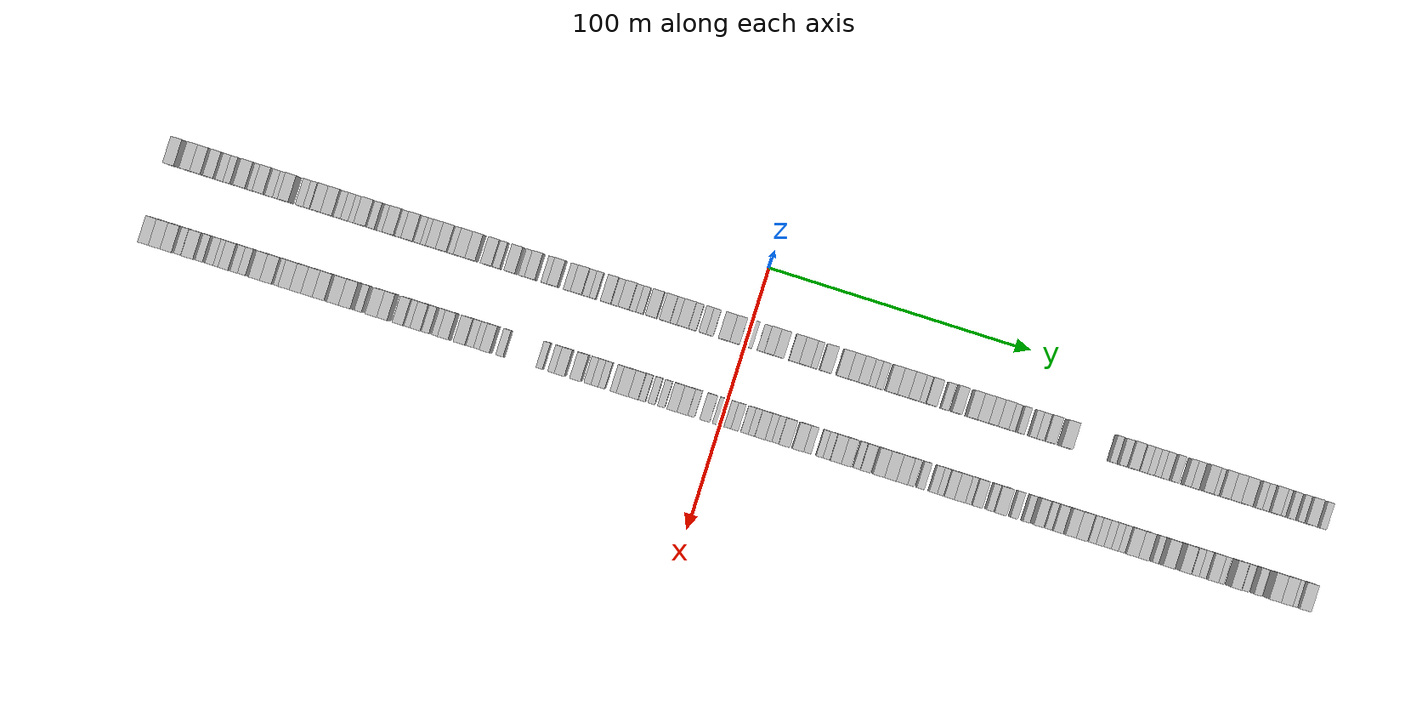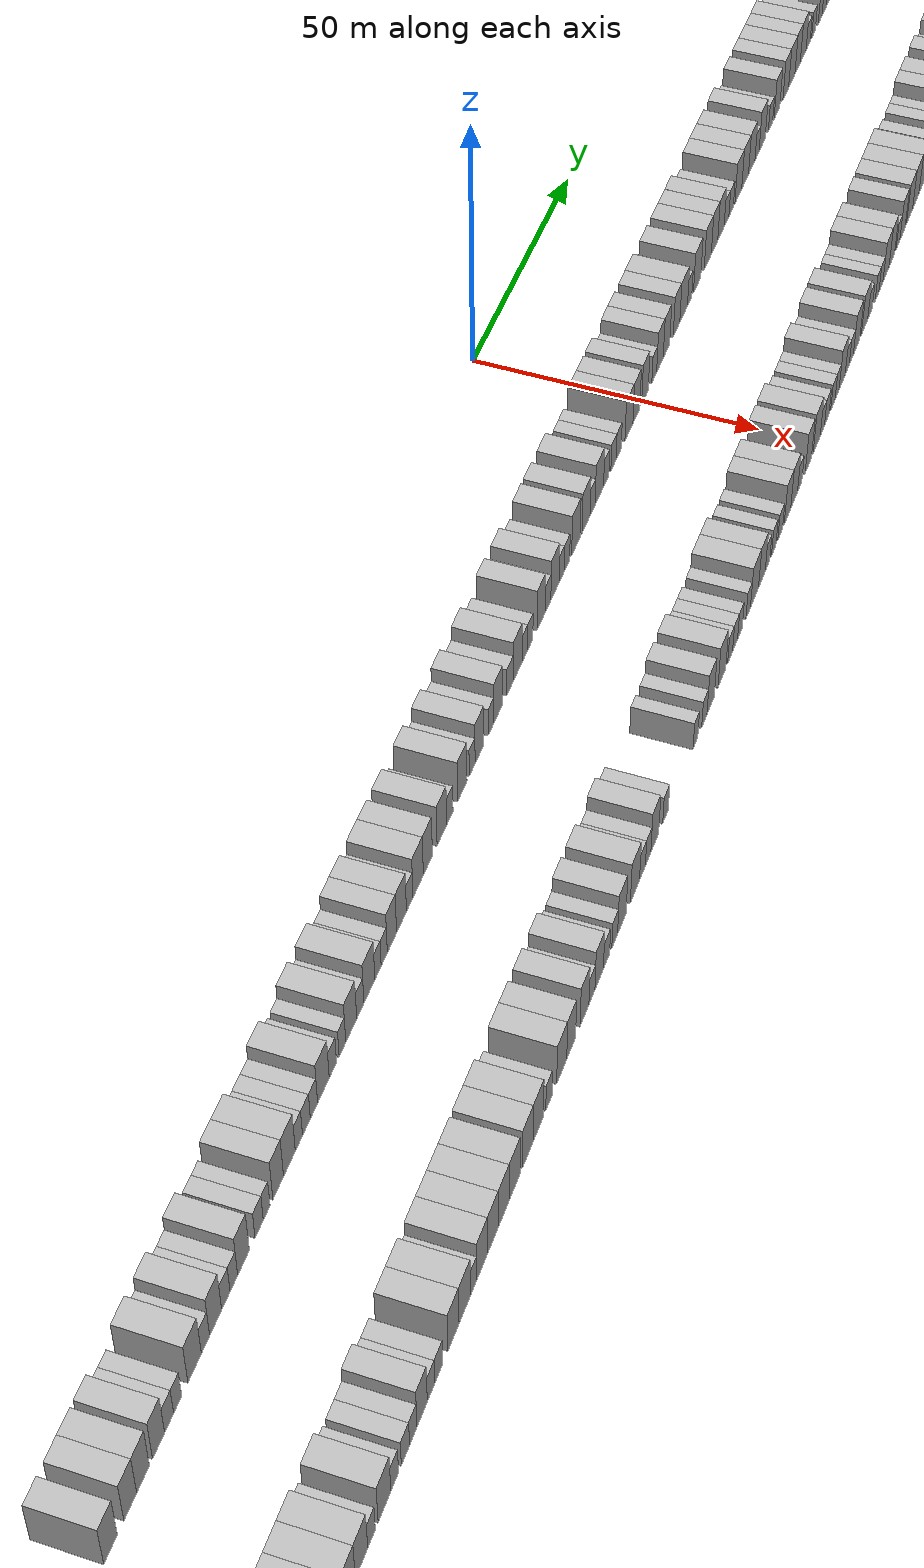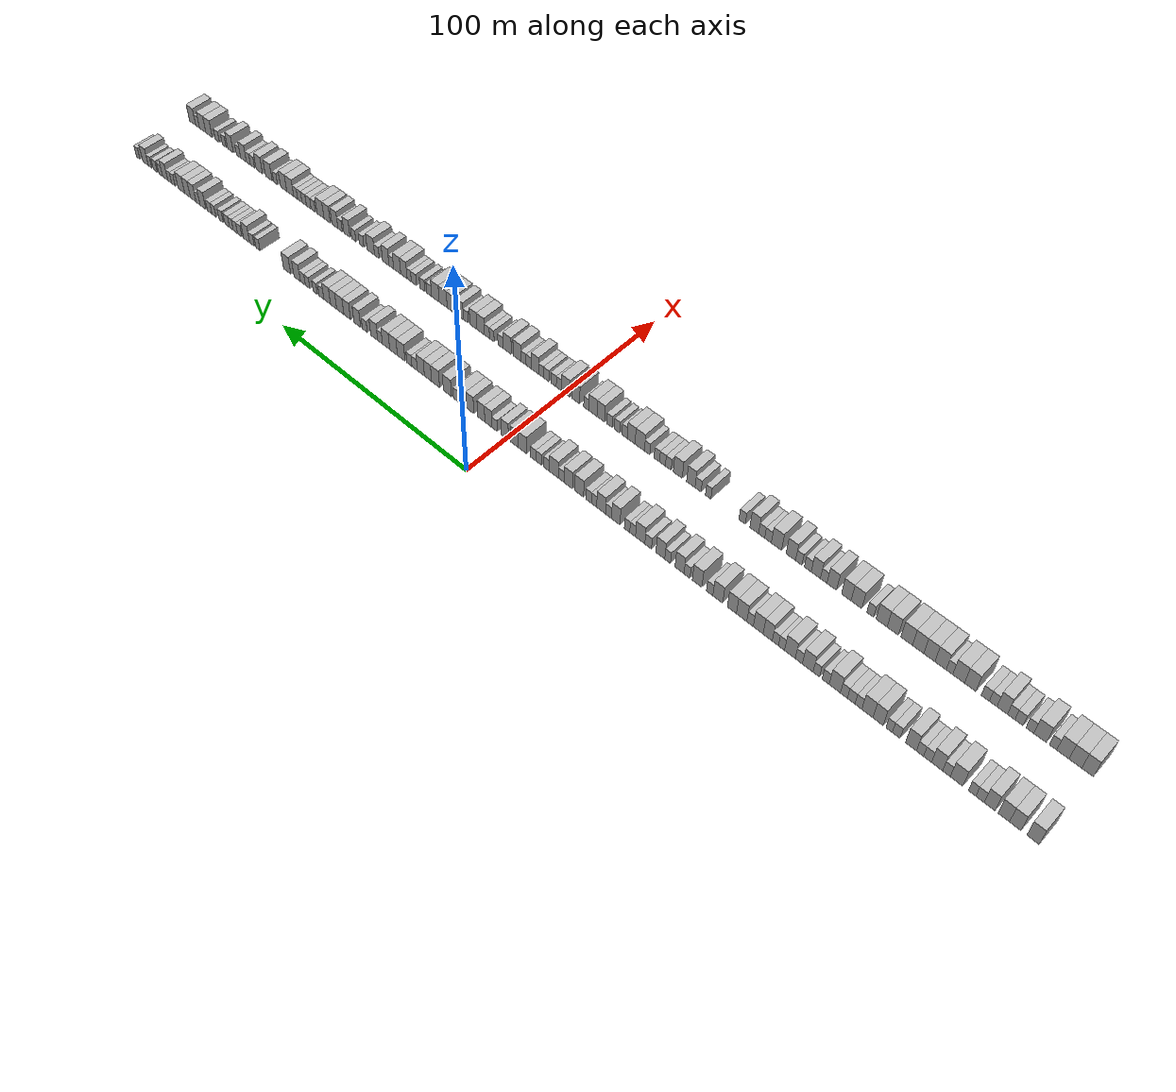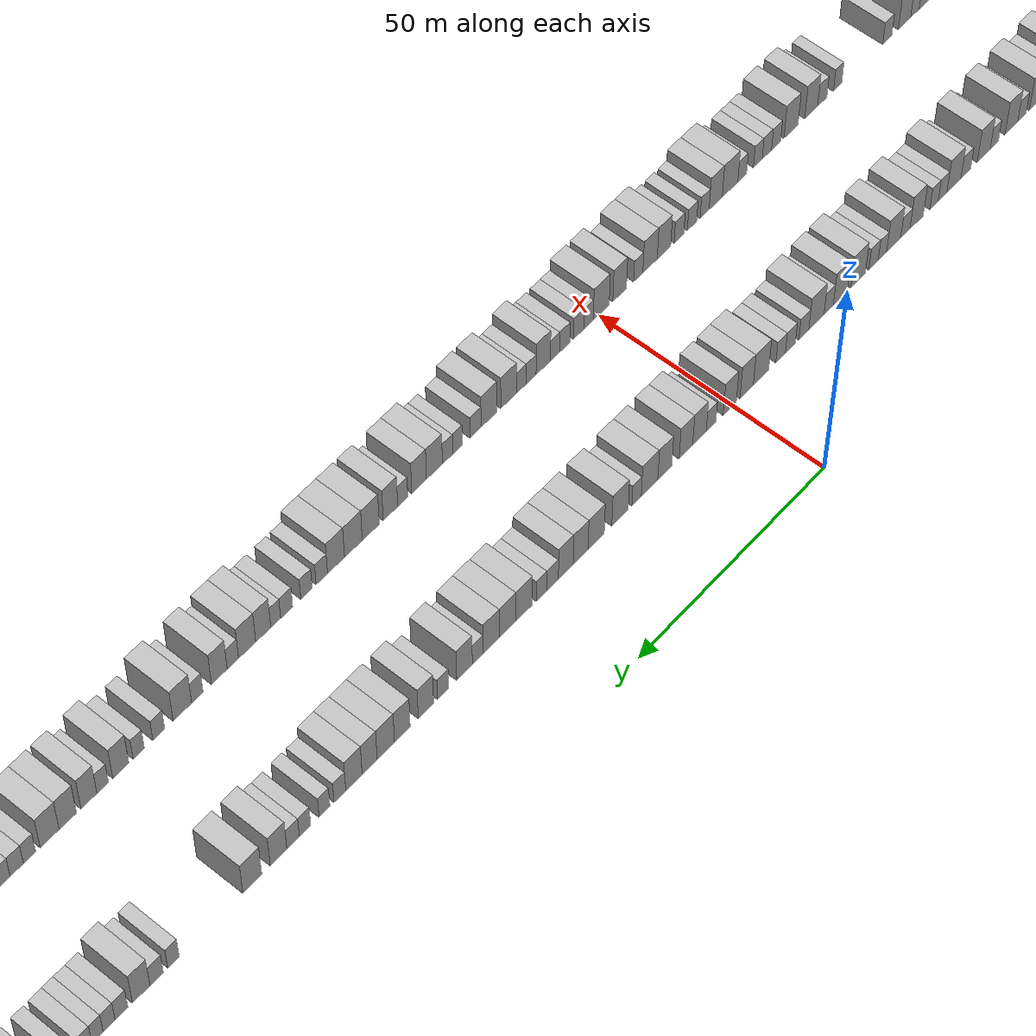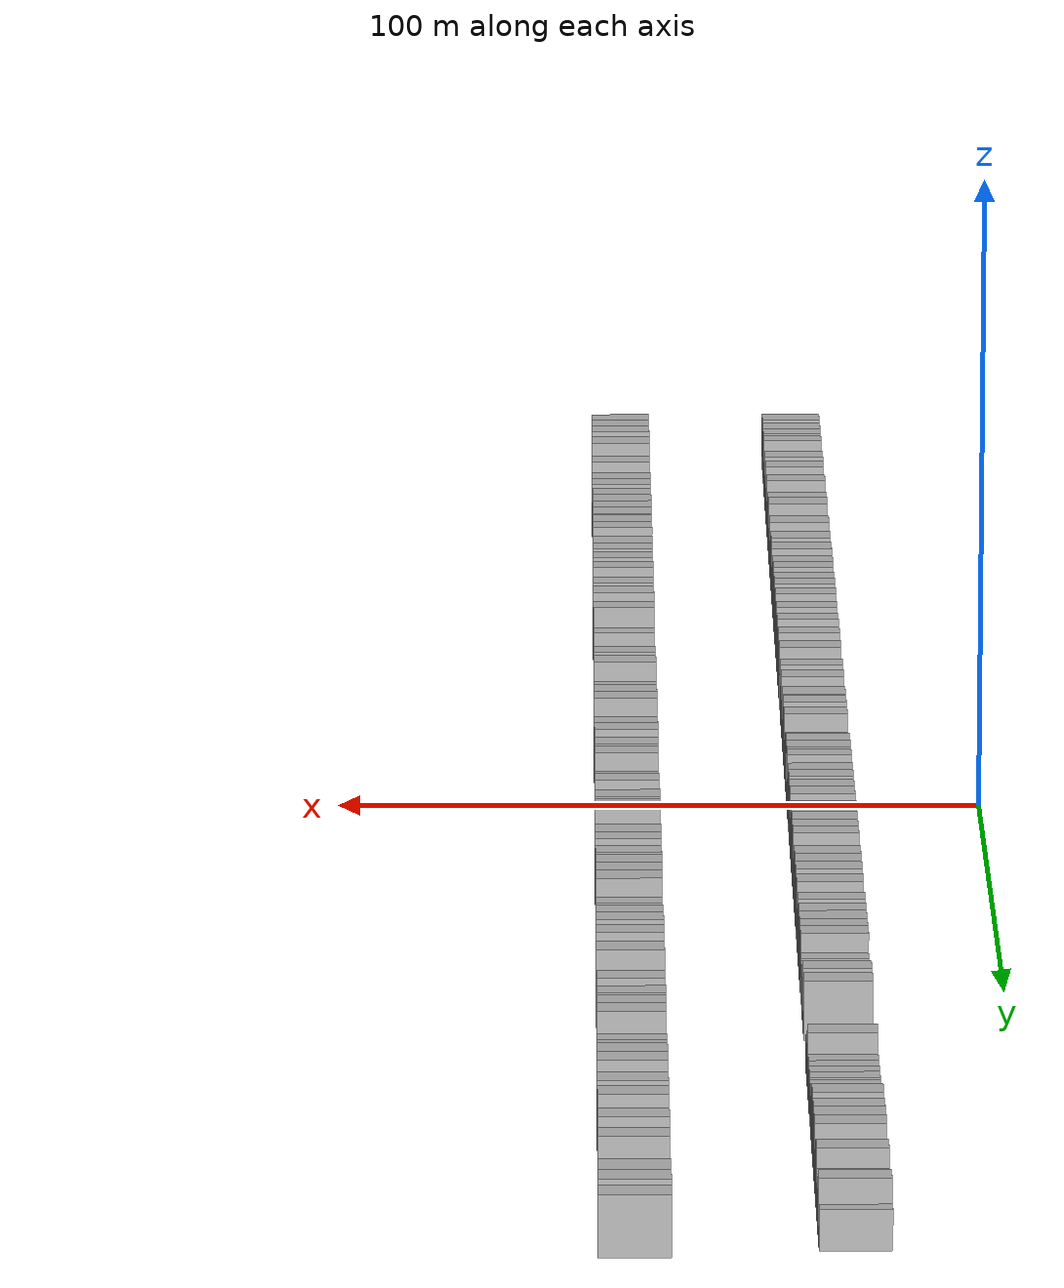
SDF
<sdf version="1.6">
 <world name="default">
  <scene>
   <sky><clouds><speed>12</speed></clouds></sky>
   <ambient>0.4 0.4 0.4 1</ambient>
   <background>0.7 0.7 0.7 1</background>
   <shadows>1</shadows>
  </scene>
  <gravity>0 0 -9.8066</gravity>
  <magnetic_field>6e-06 2.3e-05 -4.2e-05</magnetic_field>
  <physics default="0" name="default_physics" type="ode">
   <ode>
    <solver>
     <type>quick</type>
     <iters>10</iters>
     <sor>1.0</sor>
     <use_dynamic_moi_rescaling>0</use_dynamic_moi_rescaling>
    </solver>
    <constraints>
     <cfm>0</cfm>
     <erp>0.2</erp>
     <contact_max_correcting_vel>100</contact_max_correcting_vel>
     <contact_surface_layer>0.001</contact_surface_layer>
    </constraints>
   </ode>
   <max_step_size>0.004</max_step_size>
   <real_time_factor>1</real_time_factor>
   <real_time_update_rate>250</real_time_update_rate>
  </physics>
  <light name="sun" type="directional">
   <pose>0 0 10 0 0 0</pose>
   <diffuse>0.8 0.8 0.8 1</diffuse>
   <specular>0.2 0.2 0.2 1</specular>
   <attenuation>
    <range>1000</range>
    <constant>0.9</constant>
    <linear>0.01</linear>
    <quadratic>0.001</quadratic>
   </attenuation>
   <direction>-0.5 0.1 -0.9</direction>
  </light>
  <model name="building_1">
   <static>1</static>
   <pose>25.0000 -217.9095 0 0.000000 0.000000 0.000000</pose>
   <link name="link">
    <pose>0 0 4.50 0 0 0</pose>
    <collision name="collision"><geometry><box><size>10.0000 4.1810 9.0000</size></box></geometry></collision>
    <visual name="visual">
     <cast_shadows>0</cast_shadows>
     <geometry><box><size>10.0000 4.1810 9.0000</size></box></geometry>
     <material>
      <script>
       <uri>model://HANNAS_wall/materials/scripts</uri>
       <uri>model://HANNAS_wall/materials/textures</uri>
       <name>vrc/HANNAS_wall</name>
      </script>
     </material>
    </visual>
   </link>
  </model>
  <model name="building_2">
   <static>1</static>
   <pose>25.0000 -211.8305 0 0.000000 0.000000 0.000000</pose>
   <link name="link">
    <pose>0 0 4.50 0 0 0</pose>
    <collision name="collision"><geometry><box><size>10.0000 3.9770 9.0000</size></box></geometry></collision>
    <visual name="visual">
     <cast_shadows>0</cast_shadows>
     <geometry><box><size>10.0000 3.9770 9.0000</size></box></geometry>
     <material>
      <script>
       <uri>model://HANNAS_wall/materials/scripts</uri>
       <uri>model://HANNAS_wall/materials/textures</uri>
       <name>vrc/HANNAS_wall</name>
      </script>
     </material>
    </visual>
   </link>
  </model>
  <model name="building_3">
   <static>1</static>
   <pose>25.0000 -207.8415 0 0.000000 0.000000 0.000000</pose>
   <link name="link">
    <pose>0 0 4.50 0 0 0</pose>
    <collision name="collision"><geometry><box><size>10.0000 4.0009 9.0000</size></box></geometry></collision>
    <visual name="visual">
     <cast_shadows>0</cast_shadows>
     <geometry><box><size>10.0000 4.0009 9.0000</size></box></geometry>
     <material>
      <script>
       <uri>model://HANNAS_wall/materials/scripts</uri>
       <uri>model://HANNAS_wall/materials/textures</uri>
       <name>vrc/HANNAS_wall</name>
      </script>
     </material>
    </visual>
   </link>
  </model>
  <model name="building_4">
   <static>1</static>
   <pose>25.0000 -202.9239 0 0.000000 0.000000 0.000000</pose>
   <link name="link">
    <pose>0 0 4.50 0 0 0</pose>
    <collision name="collision"><geometry><box><size>10.0000 3.8345 9.0000</size></box></geometry></collision>
    <visual name="visual">
     <cast_shadows>0</cast_shadows>
     <geometry><box><size>10.0000 3.8345 9.0000</size></box></geometry>
     <material>
      <script>
       <uri>model://HANNAS_wall/materials/scripts</uri>
       <uri>model://HANNAS_wall/materials/textures</uri>
       <name>vrc/HANNAS_wall</name>
      </script>
     </material>
    </visual>
   </link>
  </model>
  <model name="building_5">
   <static>1</static>
   <pose>25.0000 -199.5439 0 0.000000 0.000000 0.000000</pose>
   <link name="link">
    <pose>0 0 3.00 0 0 0</pose>
    <collision name="collision"><geometry><box><size>10.0000 2.9255 6.0000</size></box></geometry></collision>
    <visual name="visual">
     <cast_shadows>0</cast_shadows>
     <geometry><box><size>10.0000 2.9255 6.0000</size></box></geometry>
     <material>
      <script>
       <uri>model://HANNAS_wall/materials/scripts</uri>
       <uri>model://HANNAS_wall/materials/textures</uri>
       <name>vrc/HANNAS_wall</name>
      </script>
     </material>
    </visual>
   </link>
  </model>
  <model name="building_6">
   <static>1</static>
   <pose>25.0000 -196.7667 0 0.000000 0.000000 0.000000</pose>
   <link name="link">
    <pose>0 0 3.00 0 0 0</pose>
    <collision name="collision"><geometry><box><size>10.0000 2.6289 6.0000</size></box></geometry></collision>
    <visual name="visual">
     <cast_shadows>0</cast_shadows>
     <geometry><box><size>10.0000 2.6289 6.0000</size></box></geometry>
     <material>
      <script>
       <uri>model://HANNAS_wall/materials/scripts</uri>
       <uri>model://HANNAS_wall/materials/textures</uri>
       <name>vrc/HANNAS_wall</name>
      </script>
     </material>
    </visual>
   </link>
  </model>
  <model name="building_7">
   <static>1</static>
   <pose>25.0000 -191.2194 0 0.000000 0.000000 0.000000</pose>
   <link name="link">
    <pose>0 0 4.50 0 0 0</pose>
    <collision name="collision"><geometry><box><size>10.0000 4.4657 9.0000</size></box></geometry></collision>
    <visual name="visual">
     <cast_shadows>0</cast_shadows>
     <geometry><box><size>10.0000 4.4657 9.0000</size></box></geometry>
     <material>
      <script>
       <uri>model://HANNAS_wall/materials/scripts</uri>
       <uri>model://HANNAS_wall/materials/textures</uri>
       <name>vrc/HANNAS_wall</name>
      </script>
     </material>
    </visual>
   </link>
  </model>
  <model name="building_8">
   <static>1</static>
   <pose>25.0000 -187.6018 0 0.000000 0.000000 0.000000</pose>
   <link name="link">
    <pose>0 0 3.00 0 0 0</pose>
    <collision name="collision"><geometry><box><size>10.0000 2.7696 6.0000</size></box></geometry></collision>
    <visual name="visual">
     <cast_shadows>0</cast_shadows>
     <geometry><box><size>10.0000 2.7696 6.0000</size></box></geometry>
     <material>
      <script>
       <uri>model://HANNAS_wall/materials/scripts</uri>
       <uri>model://HANNAS_wall/materials/textures</uri>
       <name>vrc/HANNAS_wall</name>
      </script>
     </material>
    </visual>
   </link>
  </model>
  <model name="building_9">
   <static>1</static>
   <pose>25.0000 -184.1889 0 0.000000 0.000000 0.000000</pose>
   <link name="link">
    <pose>0 0 4.50 0 0 0</pose>
    <collision name="collision"><geometry><box><size>10.0000 4.0561 9.0000</size></box></geometry></collision>
    <visual name="visual">
     <cast_shadows>0</cast_shadows>
     <geometry><box><size>10.0000 4.0561 9.0000</size></box></geometry>
     <material>
      <script>
       <uri>model://HANNAS_wall/materials/scripts</uri>
       <uri>model://HANNAS_wall/materials/textures</uri>
       <name>vrc/HANNAS_wall</name>
      </script>
     </material>
    </visual>
   </link>
  </model>
  <model name="building_10">
   <static>1</static>
   <pose>25.0000 -180.7169 0 0.000000 0.000000 0.000000</pose>
   <link name="link">
    <pose>0 0 3.00 0 0 0</pose>
    <collision name="collision"><geometry><box><size>10.0000 2.8880 6.0000</size></box></geometry></collision>
    <visual name="visual">
     <cast_shadows>0</cast_shadows>
     <geometry><box><size>10.0000 2.8880 6.0000</size></box></geometry>
     <material>
      <script>
       <uri>model://HANNAS_wall/materials/scripts</uri>
       <uri>model://HANNAS_wall/materials/textures</uri>
       <name>vrc/HANNAS_wall</name>
      </script>
     </material>
    </visual>
   </link>
  </model>
  <model name="building_11">
   <static>1</static>
   <pose>25.0000 -177.9663 0 0.000000 0.000000 0.000000</pose>
   <link name="link">
    <pose>0 0 3.00 0 0 0</pose>
    <collision name="collision"><geometry><box><size>10.0000 2.6132 6.0000</size></box></geometry></collision>
    <visual name="visual">
     <cast_shadows>0</cast_shadows>
     <geometry><box><size>10.0000 2.6132 6.0000</size></box></geometry>
     <material>
      <script>
       <uri>model://HANNAS_wall/materials/scripts</uri>
       <uri>model://HANNAS_wall/materials/textures</uri>
       <name>vrc/HANNAS_wall</name>
      </script>
     </material>
    </visual>
   </link>
  </model>
  <model name="building_12">
   <static>1</static>
   <pose>25.0000 -174.6368 0 0.000000 0.000000 0.000000</pose>
   <link name="link">
    <pose>0 0 4.50 0 0 0</pose>
    <collision name="collision"><geometry><box><size>10.0000 4.0458 9.0000</size></box></geometry></collision>
    <visual name="visual">
     <cast_shadows>0</cast_shadows>
     <geometry><box><size>10.0000 4.0458 9.0000</size></box></geometry>
     <material>
      <script>
       <uri>model://HANNAS_wall/materials/scripts</uri>
       <uri>model://HANNAS_wall/materials/textures</uri>
       <name>vrc/HANNAS_wall</name>
      </script>
     </material>
    </visual>
   </link>
  </model>
  <model name="building_13">
   <static>1</static>
   <pose>25.0000 -169.1580 0 0.000000 0.000000 0.000000</pose>
   <link name="link">
    <pose>0 0 3.00 0 0 0</pose>
    <collision name="collision"><geometry><box><size>10.0000 2.9118 6.0000</size></box></geometry></collision>
    <visual name="visual">
     <cast_shadows>0</cast_shadows>
     <geometry><box><size>10.0000 2.9118 6.0000</size></box></geometry>
     <material>
      <script>
       <uri>model://HANNAS_wall/materials/scripts</uri>
       <uri>model://HANNAS_wall/materials/textures</uri>
       <name>vrc/HANNAS_wall</name>
      </script>
     </material>
    </visual>
   </link>
  </model>
  <model name="building_14">
   <static>1</static>
   <pose>25.0000 -166.4994 0 0.000000 0.000000 0.000000</pose>
   <link name="link">
    <pose>0 0 3.00 0 0 0</pose>
    <collision name="collision"><geometry><box><size>10.0000 2.4055 6.0000</size></box></geometry></collision>
    <visual name="visual">
     <cast_shadows>0</cast_shadows>
     <geometry><box><size>10.0000 2.4055 6.0000</size></box></geometry>
     <material>
      <script>
       <uri>model://HANNAS_wall/materials/scripts</uri>
       <uri>model://HANNAS_wall/materials/textures</uri>
       <name>vrc/HANNAS_wall</name>
      </script>
     </material>
    </visual>
   </link>
  </model>
  <model name="building_15">
   <static>1</static>
   <pose>25.0000 -162.3699 0 0.000000 0.000000 0.000000</pose>
   <link name="link">
    <pose>0 0 4.50 0 0 0</pose>
    <collision name="collision"><geometry><box><size>10.0000 3.8535 9.0000</size></box></geometry></collision>
    <visual name="visual">
     <cast_shadows>0</cast_shadows>
     <geometry><box><size>10.0000 3.8535 9.0000</size></box></geometry>
     <material>
      <script>
       <uri>model://HANNAS_wall/materials/scripts</uri>
       <uri>model://HANNAS_wall/materials/textures</uri>
       <name>vrc/HANNAS_wall</name>
      </script>
     </material>
    </visual>
   </link>
  </model>
  <model name="building_16">
   <static>1</static>
   <pose>25.0000 -158.2993 0 0.000000 0.000000 0.000000</pose>
   <link name="link">
    <pose>0 0 4.50 0 0 0</pose>
    <collision name="collision"><geometry><box><size>10.0000 4.2877 9.0000</size></box></geometry></collision>
    <visual name="visual">
     <cast_shadows>0</cast_shadows>
     <geometry><box><size>10.0000 4.2877 9.0000</size></box></geometry>
     <material>
      <script>
       <uri>model://HANNAS_wall/materials/scripts</uri>
       <uri>model://HANNAS_wall/materials/textures</uri>
       <name>vrc/HANNAS_wall</name>
      </script>
     </material>
    </visual>
   </link>
  </model>
  <model name="building_17">
   <static>1</static>
   <pose>25.0000 -154.8249 0 0.000000 0.000000 0.000000</pose>
   <link name="link">
    <pose>0 0 3.00 0 0 0</pose>
    <collision name="collision"><geometry><box><size>10.0000 2.6612 6.0000</size></box></geometry></collision>
    <visual name="visual">
     <cast_shadows>0</cast_shadows>
     <geometry><box><size>10.0000 2.6612 6.0000</size></box></geometry>
     <material>
      <script>
       <uri>model://HANNAS_wall/materials/scripts</uri>
       <uri>model://HANNAS_wall/materials/textures</uri>
       <name>vrc/HANNAS_wall</name>
      </script>
     </material>
    </visual>
   </link>
  </model>
  <model name="building_18">
   <static>1</static>
   <pose>25.0000 -152.0456 0 0.000000 0.000000 0.000000</pose>
   <link name="link">
    <pose>0 0 3.00 0 0 0</pose>
    <collision name="collision"><geometry><box><size>10.0000 2.8976 6.0000</size></box></geometry></collision>
    <visual name="visual">
     <cast_shadows>0</cast_shadows>
     <geometry><box><size>10.0000 2.8976 6.0000</size></box></geometry>
     <material>
      <script>
       <uri>model://HANNAS_wall/materials/scripts</uri>
       <uri>model://HANNAS_wall/materials/textures</uri>
       <name>vrc/HANNAS_wall</name>
      </script>
     </material>
    </visual>
   </link>
  </model>
  <model name="building_19">
   <static>1</static>
   <pose>25.0000 -149.2381 0 0.000000 0.000000 0.000000</pose>
   <link name="link">
    <pose>0 0 3.00 0 0 0</pose>
    <collision name="collision"><geometry><box><size>10.0000 2.7174 6.0000</size></box></geometry></collision>
    <visual name="visual">
     <cast_shadows>0</cast_shadows>
     <geometry><box><size>10.0000 2.7174 6.0000</size></box></geometry>
     <material>
      <script>
       <uri>model://HANNAS_wall/materials/scripts</uri>
       <uri>model://HANNAS_wall/materials/textures</uri>
       <name>vrc/HANNAS_wall</name>
      </script>
     </material>
    </visual>
   </link>
  </model>
  <model name="building_20">
   <static>1</static>
   <pose>25.0000 -145.6842 0 0.000000 0.000000 0.000000</pose>
   <link name="link">
    <pose>0 0 4.50 0 0 0</pose>
    <collision name="collision"><geometry><box><size>10.0000 4.3903 9.0000</size></box></geometry></collision>
    <visual name="visual">
     <cast_shadows>0</cast_shadows>
     <geometry><box><size>10.0000 4.3903 9.0000</size></box></geometry>
     <material>
      <script>
       <uri>model://HANNAS_wall/materials/scripts</uri>
       <uri>model://HANNAS_wall/materials/textures</uri>
       <name>vrc/HANNAS_wall</name>
      </script>
     </material>
    </visual>
   </link>
  </model>
  <model name="building_21">
   <static>1</static>
   <pose>25.0000 -142.0989 0 0.000000 0.000000 0.000000</pose>
   <link name="link">
    <pose>0 0 3.00 0 0 0</pose>
    <collision name="collision"><geometry><box><size>10.0000 2.7802 6.0000</size></box></geometry></collision>
    <visual name="visual">
     <cast_shadows>0</cast_shadows>
     <geometry><box><size>10.0000 2.7802 6.0000</size></box></geometry>
     <material>
      <script>
       <uri>model://HANNAS_wall/materials/scripts</uri>
       <uri>model://HANNAS_wall/materials/textures</uri>
       <name>vrc/HANNAS_wall</name>
      </script>
     </material>
    </visual>
   </link>
  </model>
  <model name="building_22">
   <static>1</static>
   <pose>25.0000 -138.4294 0 0.000000 0.000000 0.000000</pose>
   <link name="link">
    <pose>0 0 3.00 0 0 0</pose>
    <collision name="collision"><geometry><box><size>10.0000 2.5588 6.0000</size></box></geometry></collision>
    <visual name="visual">
     <cast_shadows>0</cast_shadows>
     <geometry><box><size>10.0000 2.5588 6.0000</size></box></geometry>
     <material>
      <script>
       <uri>model://HANNAS_wall/materials/scripts</uri>
       <uri>model://HANNAS_wall/materials/textures</uri>
       <name>vrc/HANNAS_wall</name>
      </script>
     </material>
    </visual>
   </link>
  </model>
  <model name="building_23">
   <static>1</static>
   <pose>25.0000 -135.0135 0 0.000000 0.000000 0.000000</pose>
   <link name="link">
    <pose>0 0 4.50 0 0 0</pose>
    <collision name="collision"><geometry><box><size>10.0000 4.2731 9.0000</size></box></geometry></collision>
    <visual name="visual">
     <cast_shadows>0</cast_shadows>
     <geometry><box><size>10.0000 4.2731 9.0000</size></box></geometry>
     <material>
      <script>
       <uri>model://HANNAS_wall/materials/scripts</uri>
       <uri>model://HANNAS_wall/materials/textures</uri>
       <name>vrc/HANNAS_wall</name>
      </script>
     </material>
    </visual>
   </link>
  </model>
  <model name="building_24">
   <static>1</static>
   <pose>25.0000 -131.4598 0 0.000000 0.000000 0.000000</pose>
   <link name="link">
    <pose>0 0 3.00 0 0 0</pose>
    <collision name="collision"><geometry><box><size>10.0000 2.8342 6.0000</size></box></geometry></collision>
    <visual name="visual">
     <cast_shadows>0</cast_shadows>
     <geometry><box><size>10.0000 2.8342 6.0000</size></box></geometry>
     <material>
      <script>
       <uri>model://HANNAS_wall/materials/scripts</uri>
       <uri>model://HANNAS_wall/materials/textures</uri>
       <name>vrc/HANNAS_wall</name>
      </script>
     </material>
    </visual>
   </link>
  </model>
  <model name="building_25">
   <static>1</static>
   <pose>25.0000 -127.8671 0 0.000000 0.000000 0.000000</pose>
   <link name="link">
    <pose>0 0 4.50 0 0 0</pose>
    <collision name="collision"><geometry><box><size>10.0000 4.3512 9.0000</size></box></geometry></collision>
    <visual name="visual">
     <cast_shadows>0</cast_shadows>
     <geometry><box><size>10.0000 4.3512 9.0000</size></box></geometry>
     <material>
      <script>
       <uri>model://HANNAS_wall/materials/scripts</uri>
       <uri>model://HANNAS_wall/materials/textures</uri>
       <name>vrc/HANNAS_wall</name>
      </script>
     </material>
    </visual>
   </link>
  </model>
  <model name="building_26">
   <static>1</static>
   <pose>25.0000 -124.4405 0 0.000000 0.000000 0.000000</pose>
   <link name="link">
    <pose>0 0 3.00 0 0 0</pose>
    <collision name="collision"><geometry><box><size>10.0000 2.5020 6.0000</size></box></geometry></collision>
    <visual name="visual">
     <cast_shadows>0</cast_shadows>
     <geometry><box><size>10.0000 2.5020 6.0000</size></box></geometry>
     <material>
      <script>
       <uri>model://HANNAS_wall/materials/scripts</uri>
       <uri>model://HANNAS_wall/materials/textures</uri>
       <name>vrc/HANNAS_wall</name>
      </script>
     </material>
    </visual>
   </link>
  </model>
  <model name="building_27">
   <static>1</static>
   <pose>25.0000 -121.9420 0 0.000000 0.000000 0.000000</pose>
   <link name="link">
    <pose>0 0 3.00 0 0 0</pose>
    <collision name="collision"><geometry><box><size>10.0000 2.4951 6.0000</size></box></geometry></collision>
    <visual name="visual">
     <cast_shadows>0</cast_shadows>
     <geometry><box><size>10.0000 2.4951 6.0000</size></box></geometry>
     <material>
      <script>
       <uri>model://HANNAS_wall/materials/scripts</uri>
       <uri>model://HANNAS_wall/materials/textures</uri>
       <name>vrc/HANNAS_wall</name>
      </script>
     </material>
    </visual>
   </link>
  </model>
  <model name="building_28">
   <static>1</static>
   <pose>25.0000 -118.8082 0 0.000000 0.000000 0.000000</pose>
   <link name="link">
    <pose>0 0 4.50 0 0 0</pose>
    <collision name="collision"><geometry><box><size>10.0000 3.7726 9.0000</size></box></geometry></collision>
    <visual name="visual">
     <cast_shadows>0</cast_shadows>
     <geometry><box><size>10.0000 3.7726 9.0000</size></box></geometry>
     <material>
      <script>
       <uri>model://HANNAS_wall/materials/scripts</uri>
       <uri>model://HANNAS_wall/materials/textures</uri>
       <name>vrc/HANNAS_wall</name>
      </script>
     </material>
    </visual>
   </link>
  </model>
  <model name="building_29">
   <static>1</static>
   <pose>25.0000 -114.8955 0 0.000000 0.000000 0.000000</pose>
   <link name="link">
    <pose>0 0 4.50 0 0 0</pose>
    <collision name="collision"><geometry><box><size>10.0000 4.0526 9.0000</size></box></geometry></collision>
    <visual name="visual">
     <cast_shadows>0</cast_shadows>
     <geometry><box><size>10.0000 4.0526 9.0000</size></box></geometry>
     <material>
      <script>
       <uri>model://HANNAS_wall/materials/scripts</uri>
       <uri>model://HANNAS_wall/materials/textures</uri>
       <name>vrc/HANNAS_wall</name>
      </script>
     </material>
    </visual>
   </link>
  </model>
  <model name="building_30">
   <static>1</static>
   <pose>25.0000 -111.5190 0 0.000000 0.000000 0.000000</pose>
   <link name="link">
    <pose>0 0 3.00 0 0 0</pose>
    <collision name="collision"><geometry><box><size>10.0000 2.7004 6.0000</size></box></geometry></collision>
    <visual name="visual">
     <cast_shadows>0</cast_shadows>
     <geometry><box><size>10.0000 2.7004 6.0000</size></box></geometry>
     <material>
      <script>
       <uri>model://HANNAS_wall/materials/scripts</uri>
       <uri>model://HANNAS_wall/materials/textures</uri>
       <name>vrc/HANNAS_wall</name>
      </script>
     </material>
    </visual>
   </link>
  </model>
  <model name="building_31">
   <static>1</static>
   <pose>25.0000 -107.9925 0 0.000000 0.000000 0.000000</pose>
   <link name="link">
    <pose>0 0 4.50 0 0 0</pose>
    <collision name="collision"><geometry><box><size>10.0000 4.3526 9.0000</size></box></geometry></collision>
    <visual name="visual">
     <cast_shadows>0</cast_shadows>
     <geometry><box><size>10.0000 4.3526 9.0000</size></box></geometry>
     <material>
      <script>
       <uri>model://HANNAS_wall/materials/scripts</uri>
       <uri>model://HANNAS_wall/materials/textures</uri>
       <name>vrc/HANNAS_wall</name>
      </script>
     </material>
    </visual>
   </link>
  </model>
  <model name="building_32">
   <static>1</static>
   <pose>25.0000 -103.9009 0 0.000000 0.000000 0.000000</pose>
   <link name="link">
    <pose>0 0 4.50 0 0 0</pose>
    <collision name="collision"><geometry><box><size>10.0000 3.8305 9.0000</size></box></geometry></collision>
    <visual name="visual">
     <cast_shadows>0</cast_shadows>
     <geometry><box><size>10.0000 3.8305 9.0000</size></box></geometry>
     <material>
      <script>
       <uri>model://HANNAS_wall/materials/scripts</uri>
       <uri>model://HANNAS_wall/materials/textures</uri>
       <name>vrc/HANNAS_wall</name>
      </script>
     </material>
    </visual>
   </link>
  </model>
  <model name="building_33">
   <static>1</static>
   <pose>25.0000 -97.9165 0 0.000000 0.000000 0.000000</pose>
   <link name="link">
    <pose>0 0 4.50 0 0 0</pose>
    <collision name="collision"><geometry><box><size>10.0000 4.1384 9.0000</size></box></geometry></collision>
    <visual name="visual">
     <cast_shadows>0</cast_shadows>
     <geometry><box><size>10.0000 4.1384 9.0000</size></box></geometry>
     <material>
      <script>
       <uri>model://HANNAS_wall/materials/scripts</uri>
       <uri>model://HANNAS_wall/materials/textures</uri>
       <name>vrc/HANNAS_wall</name>
      </script>
     </material>
    </visual>
   </link>
  </model>
  <model name="building_34">
   <static>1</static>
   <pose>25.0000 -94.4695 0 0.000000 0.000000 0.000000</pose>
   <link name="link">
    <pose>0 0 3.00 0 0 0</pose>
    <collision name="collision"><geometry><box><size>10.0000 2.7556 6.0000</size></box></geometry></collision>
    <visual name="visual">
     <cast_shadows>0</cast_shadows>
     <geometry><box><size>10.0000 2.7556 6.0000</size></box></geometry>
     <material>
      <script>
       <uri>model://HANNAS_wall/materials/scripts</uri>
       <uri>model://HANNAS_wall/materials/textures</uri>
       <name>vrc/HANNAS_wall</name>
      </script>
     </material>
    </visual>
   </link>
  </model>
  <model name="building_35">
   <static>1</static>
   <pose>25.0000 -89.0252 0 0.000000 0.000000 0.000000</pose>
   <link name="link">
    <pose>0 0 4.50 0 0 0</pose>
    <collision name="collision"><geometry><box><size>10.0000 4.1331 9.0000</size></box></geometry></collision>
    <visual name="visual">
     <cast_shadows>0</cast_shadows>
     <geometry><box><size>10.0000 4.1331 9.0000</size></box></geometry>
     <material>
      <script>
       <uri>model://HANNAS_wall/materials/scripts</uri>
       <uri>model://HANNAS_wall/materials/textures</uri>
       <name>vrc/HANNAS_wall</name>
      </script>
     </material>
    </visual>
   </link>
  </model>
  <model name="building_36">
   <static>1</static>
   <pose>25.0000 -84.6537 0 0.000000 0.000000 0.000000</pose>
   <link name="link">
    <pose>0 0 3.00 0 0 0</pose>
    <collision name="collision"><geometry><box><size>10.0000 2.6100 6.0000</size></box></geometry></collision>
    <visual name="visual">
     <cast_shadows>0</cast_shadows>
     <geometry><box><size>10.0000 2.6100 6.0000</size></box></geometry>
     <material>
      <script>
       <uri>model://HANNAS_wall/materials/scripts</uri>
       <uri>model://HANNAS_wall/materials/textures</uri>
       <name>vrc/HANNAS_wall</name>
      </script>
     </material>
    </visual>
   </link>
  </model>
  <model name="building_37">
   <static>1</static>
   <pose>25.0000 -81.3792 0 0.000000 0.000000 0.000000</pose>
   <link name="link">
    <pose>0 0 4.50 0 0 0</pose>
    <collision name="collision"><geometry><box><size>10.0000 3.9389 9.0000</size></box></geometry></collision>
    <visual name="visual">
     <cast_shadows>0</cast_shadows>
     <geometry><box><size>10.0000 3.9389 9.0000</size></box></geometry>
     <material>
      <script>
       <uri>model://HANNAS_wall/materials/scripts</uri>
       <uri>model://HANNAS_wall/materials/textures</uri>
       <name>vrc/HANNAS_wall</name>
      </script>
     </material>
    </visual>
   </link>
  </model>
  <model name="building_38">
   <static>1</static>
   <pose>25.0000 -76.1478 0 0.000000 0.000000 0.000000</pose>
   <link name="link">
    <pose>0 0 3.00 0 0 0</pose>
    <collision name="collision"><geometry><box><size>10.0000 2.5238 6.0000</size></box></geometry></collision>
    <visual name="visual">
     <cast_shadows>0</cast_shadows>
     <geometry><box><size>10.0000 2.5238 6.0000</size></box></geometry>
     <material>
      <script>
       <uri>model://HANNAS_wall/materials/scripts</uri>
       <uri>model://HANNAS_wall/materials/textures</uri>
       <name>vrc/HANNAS_wall</name>
      </script>
     </material>
    </visual>
   </link>
  </model>
  <model name="building_39">
   <static>1</static>
   <pose>25.0000 -72.9089 0 0.000000 0.000000 0.000000</pose>
   <link name="link">
    <pose>0 0 4.50 0 0 0</pose>
    <collision name="collision"><geometry><box><size>10.0000 3.9540 9.0000</size></box></geometry></collision>
    <visual name="visual">
     <cast_shadows>0</cast_shadows>
     <geometry><box><size>10.0000 3.9540 9.0000</size></box></geometry>
     <material>
      <script>
       <uri>model://HANNAS_wall/materials/scripts</uri>
       <uri>model://HANNAS_wall/materials/textures</uri>
       <name>vrc/HANNAS_wall</name>
      </script>
     </material>
    </visual>
   </link>
  </model>
  <model name="building_40">
   <static>1</static>
   <pose>25.0000 -67.4504 0 0.000000 0.000000 0.000000</pose>
   <link name="link">
    <pose>0 0 3.00 0 0 0</pose>
    <collision name="collision"><geometry><box><size>10.0000 2.9631 6.0000</size></box></geometry></collision>
    <visual name="visual">
     <cast_shadows>0</cast_shadows>
     <geometry><box><size>10.0000 2.9631 6.0000</size></box></geometry>
     <material>
      <script>
       <uri>model://HANNAS_wall/materials/scripts</uri>
       <uri>model://HANNAS_wall/materials/textures</uri>
       <name>vrc/HANNAS_wall</name>
      </script>
     </material>
    </visual>
   </link>
  </model>
  <model name="building_41">
   <static>1</static>
   <pose>25.0000 -63.8523 0 0.000000 0.000000 0.000000</pose>
   <link name="link">
    <pose>0 0 4.50 0 0 0</pose>
    <collision name="collision"><geometry><box><size>10.0000 4.2330 9.0000</size></box></geometry></collision>
    <visual name="visual">
     <cast_shadows>0</cast_shadows>
     <geometry><box><size>10.0000 4.2330 9.0000</size></box></geometry>
     <material>
      <script>
       <uri>model://HANNAS_wall/materials/scripts</uri>
       <uri>model://HANNAS_wall/materials/textures</uri>
       <name>vrc/HANNAS_wall</name>
      </script>
     </material>
    </visual>
   </link>
  </model>
  <model name="building_42">
   <static>1</static>
   <pose>25.0000 -60.4268 0 0.000000 0.000000 0.000000</pose>
   <link name="link">
    <pose>0 0 3.00 0 0 0</pose>
    <collision name="collision"><geometry><box><size>10.0000 2.6180 6.0000</size></box></geometry></collision>
    <visual name="visual">
     <cast_shadows>0</cast_shadows>
     <geometry><box><size>10.0000 2.6180 6.0000</size></box></geometry>
     <material>
      <script>
       <uri>model://HANNAS_wall/materials/scripts</uri>
       <uri>model://HANNAS_wall/materials/textures</uri>
       <name>vrc/HANNAS_wall</name>
      </script>
     </material>
    </visual>
   </link>
  </model>
  <model name="building_43">
   <static>1</static>
   <pose>25.0000 -57.8759 0 0.000000 0.000000 0.000000</pose>
   <link name="link">
    <pose>0 0 3.00 0 0 0</pose>
    <collision name="collision"><geometry><box><size>10.0000 2.4838 6.0000</size></box></geometry></collision>
    <visual name="visual">
     <cast_shadows>0</cast_shadows>
     <geometry><box><size>10.0000 2.4838 6.0000</size></box></geometry>
     <material>
      <script>
       <uri>model://HANNAS_wall/materials/scripts</uri>
       <uri>model://HANNAS_wall/materials/textures</uri>
       <name>vrc/HANNAS_wall</name>
      </script>
     </material>
    </visual>
   </link>
  </model>
  <model name="building_44">
   <static>1</static>
   <pose>25.0000 -52.6735 0 0.000000 0.000000 0.000000</pose>
   <link name="link">
    <pose>0 0 4.50 0 0 0</pose>
    <collision name="collision"><geometry><box><size>10.0000 3.9210 9.0000</size></box></geometry></collision>
    <visual name="visual">
     <cast_shadows>0</cast_shadows>
     <geometry><box><size>10.0000 3.9210 9.0000</size></box></geometry>
     <material>
      <script>
       <uri>model://HANNAS_wall/materials/scripts</uri>
       <uri>model://HANNAS_wall/materials/textures</uri>
       <name>vrc/HANNAS_wall</name>
      </script>
     </material>
    </visual>
   </link>
  </model>
  <model name="building_45">
   <static>1</static>
   <pose>25.0000 -49.3237 0 0.000000 0.000000 0.000000</pose>
   <link name="link">
    <pose>0 0 3.00 0 0 0</pose>
    <collision name="collision"><geometry><box><size>10.0000 2.7787 6.0000</size></box></geometry></collision>
    <visual name="visual">
     <cast_shadows>0</cast_shadows>
     <geometry><box><size>10.0000 2.7787 6.0000</size></box></geometry>
     <material>
      <script>
       <uri>model://HANNAS_wall/materials/scripts</uri>
       <uri>model://HANNAS_wall/materials/textures</uri>
       <name>vrc/HANNAS_wall</name>
      </script>
     </material>
    </visual>
   </link>
  </model>
  <model name="building_46">
   <static>1</static>
   <pose>25.0000 -45.8711 0 0.000000 0.000000 0.000000</pose>
   <link name="link">
    <pose>0 0 4.50 0 0 0</pose>
    <collision name="collision"><geometry><box><size>10.0000 4.1265 9.0000</size></box></geometry></collision>
    <visual name="visual">
     <cast_shadows>0</cast_shadows>
     <geometry><box><size>10.0000 4.1265 9.0000</size></box></geometry>
     <material>
      <script>
       <uri>model://HANNAS_wall/materials/scripts</uri>
       <uri>model://HANNAS_wall/materials/textures</uri>
       <name>vrc/HANNAS_wall</name>
      </script>
     </material>
    </visual>
   </link>
  </model>
  <model name="building_47">
   <static>1</static>
   <pose>25.0000 -42.5730 0 0.000000 0.000000 0.000000</pose>
   <link name="link">
    <pose>0 0 3.00 0 0 0</pose>
    <collision name="collision"><geometry><box><size>10.0000 2.4697 6.0000</size></box></geometry></collision>
    <visual name="visual">
     <cast_shadows>0</cast_shadows>
     <geometry><box><size>10.0000 2.4697 6.0000</size></box></geometry>
     <material>
      <script>
       <uri>model://HANNAS_wall/materials/scripts</uri>
       <uri>model://HANNAS_wall/materials/textures</uri>
       <name>vrc/HANNAS_wall</name>
      </script>
     </material>
    </visual>
   </link>
  </model>
  <model name="building_48">
   <static>1</static>
   <pose>25.0000 -39.9853 0 0.000000 0.000000 0.000000</pose>
   <link name="link">
    <pose>0 0 3.00 0 0 0</pose>
    <collision name="collision"><geometry><box><size>10.0000 2.7059 6.0000</size></box></geometry></collision>
    <visual name="visual">
     <cast_shadows>0</cast_shadows>
     <geometry><box><size>10.0000 2.7059 6.0000</size></box></geometry>
     <material>
      <script>
       <uri>model://HANNAS_wall/materials/scripts</uri>
       <uri>model://HANNAS_wall/materials/textures</uri>
       <name>vrc/HANNAS_wall</name>
      </script>
     </material>
    </visual>
   </link>
  </model>
  <model name="building_49">
   <static>1</static>
   <pose>25.0000 -35.5125 0 0.000000 0.000000 0.000000</pose>
   <link name="link">
    <pose>0 0 4.50 0 0 0</pose>
    <collision name="collision"><geometry><box><size>10.0000 4.2397 9.0000</size></box></geometry></collision>
    <visual name="visual">
     <cast_shadows>0</cast_shadows>
     <geometry><box><size>10.0000 4.2397 9.0000</size></box></geometry>
     <material>
      <script>
       <uri>model://HANNAS_wall/materials/scripts</uri>
       <uri>model://HANNAS_wall/materials/textures</uri>
       <name>vrc/HANNAS_wall</name>
      </script>
     </material>
    </visual>
   </link>
  </model>
  <model name="building_50">
   <static>1</static>
   <pose>25.0000 -30.3605 0 0.000000 0.000000 0.000000</pose>
   <link name="link">
    <pose>0 0 4.50 0 0 0</pose>
    <collision name="collision"><geometry><box><size>10.0000 4.0643 9.0000</size></box></geometry></collision>
    <visual name="visual">
     <cast_shadows>0</cast_shadows>
     <geometry><box><size>10.0000 4.0643 9.0000</size></box></geometry>
     <material>
      <script>
       <uri>model://HANNAS_wall/materials/scripts</uri>
       <uri>model://HANNAS_wall/materials/textures</uri>
       <name>vrc/HANNAS_wall</name>
      </script>
     </material>
    </visual>
   </link>
  </model>
  <model name="building_51">
   <static>1</static>
   <pose>25.0000 -27.0049 0 0.000000 0.000000 0.000000</pose>
   <link name="link">
    <pose>0 0 3.00 0 0 0</pose>
    <collision name="collision"><geometry><box><size>10.0000 2.6468 6.0000</size></box></geometry></collision>
    <visual name="visual">
     <cast_shadows>0</cast_shadows>
     <geometry><box><size>10.0000 2.6468 6.0000</size></box></geometry>
     <material>
      <script>
       <uri>model://HANNAS_wall/materials/scripts</uri>
       <uri>model://HANNAS_wall/materials/textures</uri>
       <name>vrc/HANNAS_wall</name>
      </script>
     </material>
    </visual>
   </link>
  </model>
  <model name="building_52">
   <static>1</static>
   <pose>25.0000 -23.4937 0 0.000000 0.000000 0.000000</pose>
   <link name="link">
    <pose>0 0 4.50 0 0 0</pose>
    <collision name="collision"><geometry><box><size>10.0000 4.3756 9.0000</size></box></geometry></collision>
    <visual name="visual">
     <cast_shadows>0</cast_shadows>
     <geometry><box><size>10.0000 4.3756 9.0000</size></box></geometry>
     <material>
      <script>
       <uri>model://HANNAS_wall/materials/scripts</uri>
       <uri>model://HANNAS_wall/materials/textures</uri>
       <name>vrc/HANNAS_wall</name>
      </script>
     </material>
    </visual>
   </link>
  </model>
  <model name="building_53">
   <static>1</static>
   <pose>25.0000 -19.8978 0 0.000000 0.000000 0.000000</pose>
   <link name="link">
    <pose>0 0 3.00 0 0 0</pose>
    <collision name="collision"><geometry><box><size>10.0000 2.8161 6.0000</size></box></geometry></collision>
    <visual name="visual">
     <cast_shadows>0</cast_shadows>
     <geometry><box><size>10.0000 2.8161 6.0000</size></box></geometry>
     <material>
      <script>
       <uri>model://HANNAS_wall/materials/scripts</uri>
       <uri>model://HANNAS_wall/materials/textures</uri>
       <name>vrc/HANNAS_wall</name>
      </script>
     </material>
    </visual>
   </link>
  </model>
  <model name="building_54">
   <static>1</static>
   <pose>25.0000 -16.0875 0 0.000000 0.000000 0.000000</pose>
   <link name="link">
    <pose>0 0 3.00 0 0 0</pose>
    <collision name="collision"><geometry><box><size>10.0000 2.8045 6.0000</size></box></geometry></collision>
    <visual name="visual">
     <cast_shadows>0</cast_shadows>
     <geometry><box><size>10.0000 2.8045 6.0000</size></box></geometry>
     <material>
      <script>
       <uri>model://HANNAS_wall/materials/scripts</uri>
       <uri>model://HANNAS_wall/materials/textures</uri>
       <name>vrc/HANNAS_wall</name>
      </script>
     </material>
    </visual>
   </link>
  </model>
  <model name="building_55">
   <static>1</static>
   <pose>25.0000 -13.3362 0 0.000000 0.000000 0.000000</pose>
   <link name="link">
    <pose>0 0 3.00 0 0 0</pose>
    <collision name="collision"><geometry><box><size>10.0000 2.6982 6.0000</size></box></geometry></collision>
    <visual name="visual">
     <cast_shadows>0</cast_shadows>
     <geometry><box><size>10.0000 2.6982 6.0000</size></box></geometry>
     <material>
      <script>
       <uri>model://HANNAS_wall/materials/scripts</uri>
       <uri>model://HANNAS_wall/materials/textures</uri>
       <name>vrc/HANNAS_wall</name>
      </script>
     </material>
    </visual>
   </link>
  </model>
  <model name="building_56">
   <static>1</static>
   <pose>25.0000 -7.8339 0 0.000000 0.000000 0.000000</pose>
   <link name="link">
    <pose>0 0 4.50 0 0 0</pose>
    <collision name="collision"><geometry><box><size>10.0000 4.3064 9.0000</size></box></geometry></collision>
    <visual name="visual">
     <cast_shadows>0</cast_shadows>
     <geometry><box><size>10.0000 4.3064 9.0000</size></box></geometry>
     <material>
      <script>
       <uri>model://HANNAS_wall/materials/scripts</uri>
       <uri>model://HANNAS_wall/materials/textures</uri>
       <name>vrc/HANNAS_wall</name>
      </script>
     </material>
    </visual>
   </link>
  </model>
  <model name="building_57">
   <static>1</static>
   <pose>25.0000 -3.8198 0 0.000000 0.000000 0.000000</pose>
   <link name="link">
    <pose>0 0 4.50 0 0 0</pose>
    <collision name="collision"><geometry><box><size>10.0000 3.7216 9.0000</size></box></geometry></collision>
    <visual name="visual">
     <cast_shadows>0</cast_shadows>
     <geometry><box><size>10.0000 3.7216 9.0000</size></box></geometry>
     <material>
      <script>
       <uri>model://HANNAS_wall/materials/scripts</uri>
       <uri>model://HANNAS_wall/materials/textures</uri>
       <name>vrc/HANNAS_wall</name>
      </script>
     </material>
    </visual>
   </link>
  </model>
  <model name="building_58">
   <static>1</static>
   <pose>25.0000 0.8615 0 0.000000 0.000000 0.000000</pose>
   <link name="link">
    <pose>0 0 4.50 0 0 0</pose>
    <collision name="collision"><geometry><box><size>10.0000 3.6410 9.0000</size></box></geometry></collision>
    <visual name="visual">
     <cast_shadows>0</cast_shadows>
     <geometry><box><size>10.0000 3.6410 9.0000</size></box></geometry>
     <material>
      <script>
       <uri>model://HANNAS_wall/materials/scripts</uri>
       <uri>model://HANNAS_wall/materials/textures</uri>
       <name>vrc/HANNAS_wall</name>
      </script>
     </material>
    </visual>
   </link>
  </model>
  <model name="building_59">
   <static>1</static>
   <pose>25.0000 6.0188 0 0.000000 0.000000 0.000000</pose>
   <link name="link">
    <pose>0 0 3.00 0 0 0</pose>
    <collision name="collision"><geometry><box><size>10.0000 2.6737 6.0000</size></box></geometry></collision>
    <visual name="visual">
     <cast_shadows>0</cast_shadows>
     <geometry><box><size>10.0000 2.6737 6.0000</size></box></geometry>
     <material>
      <script>
       <uri>model://HANNAS_wall/materials/scripts</uri>
       <uri>model://HANNAS_wall/materials/textures</uri>
       <name>vrc/HANNAS_wall</name>
      </script>
     </material>
    </visual>
   </link>
  </model>
  <model name="building_60">
   <static>1</static>
   <pose>25.0000 9.2011 0 0.000000 0.000000 0.000000</pose>
   <link name="link">
    <pose>0 0 4.50 0 0 0</pose>
    <collision name="collision"><geometry><box><size>10.0000 3.6910 9.0000</size></box></geometry></collision>
    <visual name="visual">
     <cast_shadows>0</cast_shadows>
     <geometry><box><size>10.0000 3.6910 9.0000</size></box></geometry>
     <material>
      <script>
       <uri>model://HANNAS_wall/materials/scripts</uri>
       <uri>model://HANNAS_wall/materials/textures</uri>
       <name>vrc/HANNAS_wall</name>
      </script>
     </material>
    </visual>
   </link>
  </model>
  <model name="building_61">
   <static>1</static>
   <pose>25.0000 12.8817 0 0.000000 0.000000 0.000000</pose>
   <link name="link">
    <pose>0 0 4.50 0 0 0</pose>
    <collision name="collision"><geometry><box><size>10.0000 3.6702 9.0000</size></box></geometry></collision>
    <visual name="visual">
     <cast_shadows>0</cast_shadows>
     <geometry><box><size>10.0000 3.6702 9.0000</size></box></geometry>
     <material>
      <script>
       <uri>model://HANNAS_wall/materials/scripts</uri>
       <uri>model://HANNAS_wall/materials/textures</uri>
       <name>vrc/HANNAS_wall</name>
      </script>
     </material>
    </visual>
   </link>
  </model>
  <model name="building_62">
   <static>1</static>
   <pose>25.0000 18.6023 0 0.000000 0.000000 0.000000</pose>
   <link name="link">
    <pose>0 0 4.50 0 0 0</pose>
    <collision name="collision"><geometry><box><size>10.0000 3.7709 9.0000</size></box></geometry></collision>
    <visual name="visual">
     <cast_shadows>0</cast_shadows>
     <geometry><box><size>10.0000 3.7709 9.0000</size></box></geometry>
     <material>
      <script>
       <uri>model://HANNAS_wall/materials/scripts</uri>
       <uri>model://HANNAS_wall/materials/textures</uri>
       <name>vrc/HANNAS_wall</name>
      </script>
     </material>
    </visual>
   </link>
  </model>
  <model name="building_63">
   <static>1</static>
   <pose>25.0000 22.7025 0 0.000000 0.000000 0.000000</pose>
   <link name="link">
    <pose>0 0 4.50 0 0 0</pose>
    <collision name="collision"><geometry><box><size>10.0000 4.4295 9.0000</size></box></geometry></collision>
    <visual name="visual">
     <cast_shadows>0</cast_shadows>
     <geometry><box><size>10.0000 4.4295 9.0000</size></box></geometry>
     <material>
      <script>
       <uri>model://HANNAS_wall/materials/scripts</uri>
       <uri>model://HANNAS_wall/materials/textures</uri>
       <name>vrc/HANNAS_wall</name>
      </script>
     </material>
    </visual>
   </link>
  </model>
  <model name="building_64">
   <static>1</static>
   <pose>25.0000 26.1662 0 0.000000 0.000000 0.000000</pose>
   <link name="link">
    <pose>0 0 3.00 0 0 0</pose>
    <collision name="collision"><geometry><box><size>10.0000 2.4980 6.0000</size></box></geometry></collision>
    <visual name="visual">
     <cast_shadows>0</cast_shadows>
     <geometry><box><size>10.0000 2.4980 6.0000</size></box></geometry>
     <material>
      <script>
       <uri>model://HANNAS_wall/materials/scripts</uri>
       <uri>model://HANNAS_wall/materials/textures</uri>
       <name>vrc/HANNAS_wall</name>
      </script>
     </material>
    </visual>
   </link>
  </model>
  <model name="building_65">
   <static>1</static>
   <pose>25.0000 30.5811 0 0.000000 0.000000 0.000000</pose>
   <link name="link">
    <pose>0 0 4.50 0 0 0</pose>
    <collision name="collision"><geometry><box><size>10.0000 4.3316 9.0000</size></box></geometry></collision>
    <visual name="visual">
     <cast_shadows>0</cast_shadows>
     <geometry><box><size>10.0000 4.3316 9.0000</size></box></geometry>
     <material>
      <script>
       <uri>model://HANNAS_wall/materials/scripts</uri>
       <uri>model://HANNAS_wall/materials/textures</uri>
       <name>vrc/HANNAS_wall</name>
      </script>
     </material>
    </visual>
   </link>
  </model>
  <model name="building_66">
   <static>1</static>
   <pose>25.0000 36.8752 0 0.000000 0.000000 0.000000</pose>
   <link name="link">
    <pose>0 0 4.50 0 0 0</pose>
    <collision name="collision"><geometry><box><size>10.0000 4.2566 9.0000</size></box></geometry></collision>
    <visual name="visual">
     <cast_shadows>0</cast_shadows>
     <geometry><box><size>10.0000 4.2566 9.0000</size></box></geometry>
     <material>
      <script>
       <uri>model://HANNAS_wall/materials/scripts</uri>
       <uri>model://HANNAS_wall/materials/textures</uri>
       <name>vrc/HANNAS_wall</name>
      </script>
     </material>
    </visual>
   </link>
  </model>
  <model name="building_67">
   <static>1</static>
   <pose>25.0000 40.9402 0 0.000000 0.000000 0.000000</pose>
   <link name="link">
    <pose>0 0 4.50 0 0 0</pose>
    <collision name="collision"><geometry><box><size>10.0000 3.8733 9.0000</size></box></geometry></collision>
    <visual name="visual">
     <cast_shadows>0</cast_shadows>
     <geometry><box><size>10.0000 3.8733 9.0000</size></box></geometry>
     <material>
      <script>
       <uri>model://HANNAS_wall/materials/scripts</uri>
       <uri>model://HANNAS_wall/materials/textures</uri>
       <name>vrc/HANNAS_wall</name>
      </script>
     </material>
    </visual>
   </link>
  </model>
  <model name="building_68">
   <static>1</static>
   <pose>25.0000 44.8084 0 0.000000 0.000000 0.000000</pose>
   <link name="link">
    <pose>0 0 4.50 0 0 0</pose>
    <collision name="collision"><geometry><box><size>10.0000 3.8630 9.0000</size></box></geometry></collision>
    <visual name="visual">
     <cast_shadows>0</cast_shadows>
     <geometry><box><size>10.0000 3.8630 9.0000</size></box></geometry>
     <material>
      <script>
       <uri>model://HANNAS_wall/materials/scripts</uri>
       <uri>model://HANNAS_wall/materials/textures</uri>
       <name>vrc/HANNAS_wall</name>
      </script>
     </material>
    </visual>
   </link>
  </model>
  <model name="building_69">
   <static>1</static>
   <pose>25.0000 48.2210 0 0.000000 0.000000 0.000000</pose>
   <link name="link">
    <pose>0 0 3.00 0 0 0</pose>
    <collision name="collision"><geometry><box><size>10.0000 2.9623 6.0000</size></box></geometry></collision>
    <visual name="visual">
     <cast_shadows>0</cast_shadows>
     <geometry><box><size>10.0000 2.9623 6.0000</size></box></geometry>
     <material>
      <script>
       <uri>model://HANNAS_wall/materials/scripts</uri>
       <uri>model://HANNAS_wall/materials/textures</uri>
       <name>vrc/HANNAS_wall</name>
      </script>
     </material>
    </visual>
   </link>
  </model>
  <model name="building_70">
   <static>1</static>
   <pose>25.0000 51.0767 0 0.000000 0.000000 0.000000</pose>
   <link name="link">
    <pose>0 0 3.00 0 0 0</pose>
    <collision name="collision"><geometry><box><size>10.0000 2.7492 6.0000</size></box></geometry></collision>
    <visual name="visual">
     <cast_shadows>0</cast_shadows>
     <geometry><box><size>10.0000 2.7492 6.0000</size></box></geometry>
     <material>
      <script>
       <uri>model://HANNAS_wall/materials/scripts</uri>
       <uri>model://HANNAS_wall/materials/textures</uri>
       <name>vrc/HANNAS_wall</name>
      </script>
     </material>
    </visual>
   </link>
  </model>
  <model name="building_71">
   <static>1</static>
   <pose>25.0000 55.5530 0 0.000000 0.000000 0.000000</pose>
   <link name="link">
    <pose>0 0 4.50 0 0 0</pose>
    <collision name="collision"><geometry><box><size>10.0000 4.2034 9.0000</size></box></geometry></collision>
    <visual name="visual">
     <cast_shadows>0</cast_shadows>
     <geometry><box><size>10.0000 4.2034 9.0000</size></box></geometry>
     <material>
      <script>
       <uri>model://HANNAS_wall/materials/scripts</uri>
       <uri>model://HANNAS_wall/materials/textures</uri>
       <name>vrc/HANNAS_wall</name>
      </script>
     </material>
    </visual>
   </link>
  </model>
  <model name="building_72">
   <static>1</static>
   <pose>25.0000 59.7783 0 0.000000 0.000000 0.000000</pose>
   <link name="link">
    <pose>0 0 4.50 0 0 0</pose>
    <collision name="collision"><geometry><box><size>10.0000 4.2473 9.0000</size></box></geometry></collision>
    <visual name="visual">
     <cast_shadows>0</cast_shadows>
     <geometry><box><size>10.0000 4.2473 9.0000</size></box></geometry>
     <material>
      <script>
       <uri>model://HANNAS_wall/materials/scripts</uri>
       <uri>model://HANNAS_wall/materials/textures</uri>
       <name>vrc/HANNAS_wall</name>
      </script>
     </material>
    </visual>
   </link>
  </model>
  <model name="building_73">
   <static>1</static>
   <pose>25.0000 63.9522 0 0.000000 0.000000 0.000000</pose>
   <link name="link">
    <pose>0 0 4.50 0 0 0</pose>
    <collision name="collision"><geometry><box><size>10.0000 4.1004 9.0000</size></box></geometry></collision>
    <visual name="visual">
     <cast_shadows>0</cast_shadows>
     <geometry><box><size>10.0000 4.1004 9.0000</size></box></geometry>
     <material>
      <script>
       <uri>model://HANNAS_wall/materials/scripts</uri>
       <uri>model://HANNAS_wall/materials/textures</uri>
       <name>vrc/HANNAS_wall</name>
      </script>
     </material>
    </visual>
   </link>
  </model>
  <model name="building_74">
   <static>1</static>
   <pose>25.0000 67.3389 0 0.000000 0.000000 0.000000</pose>
   <link name="link">
    <pose>0 0 3.00 0 0 0</pose>
    <collision name="collision"><geometry><box><size>10.0000 2.6730 6.0000</size></box></geometry></collision>
    <visual name="visual">
     <cast_shadows>0</cast_shadows>
     <geometry><box><size>10.0000 2.6730 6.0000</size></box></geometry>
     <material>
      <script>
       <uri>model://HANNAS_wall/materials/scripts</uri>
       <uri>model://HANNAS_wall/materials/textures</uri>
       <name>vrc/HANNAS_wall</name>
      </script>
     </material>
    </visual>
   </link>
  </model>
  <model name="building_75">
   <static>1</static>
   <pose>25.0000 70.6305 0 0.000000 0.000000 0.000000</pose>
   <link name="link">
    <pose>0 0 4.50 0 0 0</pose>
    <collision name="collision"><geometry><box><size>10.0000 3.9102 9.0000</size></box></geometry></collision>
    <visual name="visual">
     <cast_shadows>0</cast_shadows>
     <geometry><box><size>10.0000 3.9102 9.0000</size></box></geometry>
     <material>
      <script>
       <uri>model://HANNAS_wall/materials/scripts</uri>
       <uri>model://HANNAS_wall/materials/textures</uri>
       <name>vrc/HANNAS_wall</name>
      </script>
     </material>
    </visual>
   </link>
  </model>
  <model name="building_76">
   <static>1</static>
   <pose>25.0000 75.9710 0 0.000000 0.000000 0.000000</pose>
   <link name="link">
    <pose>0 0 3.00 0 0 0</pose>
    <collision name="collision"><geometry><box><size>10.0000 2.7708 6.0000</size></box></geometry></collision>
    <visual name="visual">
     <cast_shadows>0</cast_shadows>
     <geometry><box><size>10.0000 2.7708 6.0000</size></box></geometry>
     <material>
      <script>
       <uri>model://HANNAS_wall/materials/scripts</uri>
       <uri>model://HANNAS_wall/materials/textures</uri>
       <name>vrc/HANNAS_wall</name>
      </script>
     </material>
    </visual>
   </link>
  </model>
  <model name="building_77">
   <static>1</static>
   <pose>25.0000 80.2393 0 0.000000 0.000000 0.000000</pose>
   <link name="link">
    <pose>0 0 4.50 0 0 0</pose>
    <collision name="collision"><geometry><box><size>10.0000 3.7657 9.0000</size></box></geometry></collision>
    <visual name="visual">
     <cast_shadows>0</cast_shadows>
     <geometry><box><size>10.0000 3.7657 9.0000</size></box></geometry>
     <material>
      <script>
       <uri>model://HANNAS_wall/materials/scripts</uri>
       <uri>model://HANNAS_wall/materials/textures</uri>
       <name>vrc/HANNAS_wall</name>
      </script>
     </material>
    </visual>
   </link>
  </model>
  <model name="building_78">
   <static>1</static>
   <pose>25.0000 86.0371 0 0.000000 0.000000 0.000000</pose>
   <link name="link">
    <pose>0 0 4.50 0 0 0</pose>
    <collision name="collision"><geometry><box><size>10.0000 3.8299 9.0000</size></box></geometry></collision>
    <visual name="visual">
     <cast_shadows>0</cast_shadows>
     <geometry><box><size>10.0000 3.8299 9.0000</size></box></geometry>
     <material>
      <script>
       <uri>model://HANNAS_wall/materials/scripts</uri>
       <uri>model://HANNAS_wall/materials/textures</uri>
       <name>vrc/HANNAS_wall</name>
      </script>
     </material>
    </visual>
   </link>
  </model>
  <model name="building_79">
   <static>1</static>
   <pose>25.0000 90.0652 0 0.000000 0.000000 0.000000</pose>
   <link name="link">
    <pose>0 0 4.50 0 0 0</pose>
    <collision name="collision"><geometry><box><size>10.0000 4.2263 9.0000</size></box></geometry></collision>
    <visual name="visual">
     <cast_shadows>0</cast_shadows>
     <geometry><box><size>10.0000 4.2263 9.0000</size></box></geometry>
     <material>
      <script>
       <uri>model://HANNAS_wall/materials/scripts</uri>
       <uri>model://HANNAS_wall/materials/textures</uri>
       <name>vrc/HANNAS_wall</name>
      </script>
     </material>
    </visual>
   </link>
  </model>
  <model name="building_80">
   <static>1</static>
   <pose>25.0000 93.9865 0 0.000000 0.000000 0.000000</pose>
   <link name="link">
    <pose>0 0 4.50 0 0 0</pose>
    <collision name="collision"><geometry><box><size>10.0000 3.6165 9.0000</size></box></geometry></collision>
    <visual name="visual">
     <cast_shadows>0</cast_shadows>
     <geometry><box><size>10.0000 3.6165 9.0000</size></box></geometry>
     <material>
      <script>
       <uri>model://HANNAS_wall/materials/scripts</uri>
       <uri>model://HANNAS_wall/materials/textures</uri>
       <name>vrc/HANNAS_wall</name>
      </script>
     </material>
    </visual>
   </link>
  </model>
  <model name="building_81">
   <static>1</static>
   <pose>25.0000 97.7673 0 0.000000 0.000000 0.000000</pose>
   <link name="link">
    <pose>0 0 4.50 0 0 0</pose>
    <collision name="collision"><geometry><box><size>10.0000 3.9451 9.0000</size></box></geometry></collision>
    <visual name="visual">
     <cast_shadows>0</cast_shadows>
     <geometry><box><size>10.0000 3.9451 9.0000</size></box></geometry>
     <material>
      <script>
       <uri>model://HANNAS_wall/materials/scripts</uri>
       <uri>model://HANNAS_wall/materials/textures</uri>
       <name>vrc/HANNAS_wall</name>
      </script>
     </material>
    </visual>
   </link>
  </model>
  <model name="building_82">
   <static>1</static>
   <pose>25.0000 101.1397 0 0.000000 0.000000 0.000000</pose>
   <link name="link">
    <pose>0 0 3.00 0 0 0</pose>
    <collision name="collision"><geometry><box><size>10.0000 2.7997 6.0000</size></box></geometry></collision>
    <visual name="visual">
     <cast_shadows>0</cast_shadows>
     <geometry><box><size>10.0000 2.7997 6.0000</size></box></geometry>
     <material>
      <script>
       <uri>model://HANNAS_wall/materials/scripts</uri>
       <uri>model://HANNAS_wall/materials/textures</uri>
       <name>vrc/HANNAS_wall</name>
      </script>
     </material>
    </visual>
   </link>
  </model>
  <model name="building_83">
   <static>1</static>
   <pose>25.0000 104.8327 0 0.000000 0.000000 0.000000</pose>
   <link name="link">
    <pose>0 0 3.00 0 0 0</pose>
    <collision name="collision"><geometry><box><size>10.0000 2.5863 6.0000</size></box></geometry></collision>
    <visual name="visual">
     <cast_shadows>0</cast_shadows>
     <geometry><box><size>10.0000 2.5863 6.0000</size></box></geometry>
     <material>
      <script>
       <uri>model://HANNAS_wall/materials/scripts</uri>
       <uri>model://HANNAS_wall/materials/textures</uri>
       <name>vrc/HANNAS_wall</name>
      </script>
     </material>
    </visual>
   </link>
  </model>
  <model name="building_84">
   <static>1</static>
   <pose>25.0000 109.4549 0 0.000000 0.000000 0.000000</pose>
   <link name="link">
    <pose>0 0 3.00 0 0 0</pose>
    <collision name="collision"><geometry><box><size>10.0000 2.6581 6.0000</size></box></geometry></collision>
    <visual name="visual">
     <cast_shadows>0</cast_shadows>
     <geometry><box><size>10.0000 2.6581 6.0000</size></box></geometry>
     <material>
      <script>
       <uri>model://HANNAS_wall/materials/scripts</uri>
       <uri>model://HANNAS_wall/materials/textures</uri>
       <name>vrc/HANNAS_wall</name>
      </script>
     </material>
    </visual>
   </link>
  </model>
  <model name="building_85">
   <static>1</static>
   <pose>25.0000 112.2626 0 0.000000 0.000000 0.000000</pose>
   <link name="link">
    <pose>0 0 3.00 0 0 0</pose>
    <collision name="collision"><geometry><box><size>10.0000 2.9574 6.0000</size></box></geometry></collision>
    <visual name="visual">
     <cast_shadows>0</cast_shadows>
     <geometry><box><size>10.0000 2.9574 6.0000</size></box></geometry>
     <material>
      <script>
       <uri>model://HANNAS_wall/materials/scripts</uri>
       <uri>model://HANNAS_wall/materials/textures</uri>
       <name>vrc/HANNAS_wall</name>
      </script>
     </material>
    </visual>
   </link>
  </model>
  <model name="building_86">
   <static>1</static>
   <pose>25.0000 115.6789 0 0.000000 0.000000 0.000000</pose>
   <link name="link">
    <pose>0 0 4.50 0 0 0</pose>
    <collision name="collision"><geometry><box><size>10.0000 3.8751 9.0000</size></box></geometry></collision>
    <visual name="visual">
     <cast_shadows>0</cast_shadows>
     <geometry><box><size>10.0000 3.8751 9.0000</size></box></geometry>
     <material>
      <script>
       <uri>model://HANNAS_wall/materials/scripts</uri>
       <uri>model://HANNAS_wall/materials/textures</uri>
       <name>vrc/HANNAS_wall</name>
      </script>
     </material>
    </visual>
   </link>
  </model>
  <model name="building_87">
   <static>1</static>
   <pose>25.0000 121.8130 0 0.000000 0.000000 0.000000</pose>
   <link name="link">
    <pose>0 0 4.50 0 0 0</pose>
    <collision name="collision"><geometry><box><size>10.0000 4.3932 9.0000</size></box></geometry></collision>
    <visual name="visual">
     <cast_shadows>0</cast_shadows>
     <geometry><box><size>10.0000 4.3932 9.0000</size></box></geometry>
     <material>
      <script>
       <uri>model://HANNAS_wall/materials/scripts</uri>
       <uri>model://HANNAS_wall/materials/textures</uri>
       <name>vrc/HANNAS_wall</name>
      </script>
     </material>
    </visual>
   </link>
  </model>
  <model name="building_88">
   <static>1</static>
   <pose>25.0000 139.8758 0 0.000000 0.000000 0.000000</pose>
   <link name="link">
    <pose>0 0 3.00 0 0 0</pose>
    <collision name="collision"><geometry><box><size>10.0000 2.5774 6.0000</size></box></geometry></collision>
    <visual name="visual">
     <cast_shadows>0</cast_shadows>
     <geometry><box><size>10.0000 2.5774 6.0000</size></box></geometry>
     <material>
      <script>
       <uri>model://HANNAS_wall/materials/scripts</uri>
       <uri>model://HANNAS_wall/materials/textures</uri>
       <name>vrc/HANNAS_wall</name>
      </script>
     </material>
    </visual>
   </link>
  </model>
  <model name="building_89">
   <static>1</static>
   <pose>25.0000 143.6595 0 0.000000 0.000000 0.000000</pose>
   <link name="link">
    <pose>0 0 3.00 0 0 0</pose>
    <collision name="collision"><geometry><box><size>10.0000 2.9900 6.0000</size></box></geometry></collision>
    <visual name="visual">
     <cast_shadows>0</cast_shadows>
     <geometry><box><size>10.0000 2.9900 6.0000</size></box></geometry>
     <material>
      <script>
       <uri>model://HANNAS_wall/materials/scripts</uri>
       <uri>model://HANNAS_wall/materials/textures</uri>
       <name>vrc/HANNAS_wall</name>
      </script>
     </material>
    </visual>
   </link>
  </model>
  <model name="building_90">
   <static>1</static>
   <pose>25.0000 147.1095 0 0.000000 0.000000 0.000000</pose>
   <link name="link">
    <pose>0 0 4.50 0 0 0</pose>
    <collision name="collision"><geometry><box><size>10.0000 3.9099 9.0000</size></box></geometry></collision>
    <visual name="visual">
     <cast_shadows>0</cast_shadows>
     <geometry><box><size>10.0000 3.9099 9.0000</size></box></geometry>
     <material>
      <script>
       <uri>model://HANNAS_wall/materials/scripts</uri>
       <uri>model://HANNAS_wall/materials/textures</uri>
       <name>vrc/HANNAS_wall</name>
      </script>
     </material>
    </visual>
   </link>
  </model>
  <model name="building_91">
   <static>1</static>
   <pose>25.0000 151.4833 0 0.000000 0.000000 0.000000</pose>
   <link name="link">
    <pose>0 0 3.00 0 0 0</pose>
    <collision name="collision"><geometry><box><size>10.0000 2.8377 6.0000</size></box></geometry></collision>
    <visual name="visual">
     <cast_shadows>0</cast_shadows>
     <geometry><box><size>10.0000 2.8377 6.0000</size></box></geometry>
     <material>
      <script>
       <uri>model://HANNAS_wall/materials/scripts</uri>
       <uri>model://HANNAS_wall/materials/textures</uri>
       <name>vrc/HANNAS_wall</name>
      </script>
     </material>
    </visual>
   </link>
  </model>
  <model name="building_92">
   <static>1</static>
   <pose>25.0000 154.2225 0 0.000000 0.000000 0.000000</pose>
   <link name="link">
    <pose>0 0 3.00 0 0 0</pose>
    <collision name="collision"><geometry><box><size>10.0000 2.6409 6.0000</size></box></geometry></collision>
    <visual name="visual">
     <cast_shadows>0</cast_shadows>
     <geometry><box><size>10.0000 2.6409 6.0000</size></box></geometry>
     <material>
      <script>
       <uri>model://HANNAS_wall/materials/scripts</uri>
       <uri>model://HANNAS_wall/materials/textures</uri>
       <name>vrc/HANNAS_wall</name>
      </script>
     </material>
    </visual>
   </link>
  </model>
  <model name="building_93">
   <static>1</static>
   <pose>25.0000 156.7780 0 0.000000 0.000000 0.000000</pose>
   <link name="link">
    <pose>0 0 3.00 0 0 0</pose>
    <collision name="collision"><geometry><box><size>10.0000 2.4701 6.0000</size></box></geometry></collision>
    <visual name="visual">
     <cast_shadows>0</cast_shadows>
     <geometry><box><size>10.0000 2.4701 6.0000</size></box></geometry>
     <material>
      <script>
       <uri>model://HANNAS_wall/materials/scripts</uri>
       <uri>model://HANNAS_wall/materials/textures</uri>
       <name>vrc/HANNAS_wall</name>
      </script>
     </material>
    </visual>
   </link>
  </model>
  <model name="building_94">
   <static>1</static>
   <pose>25.0000 159.4873 0 0.000000 0.000000 0.000000</pose>
   <link name="link">
    <pose>0 0 3.00 0 0 0</pose>
    <collision name="collision"><geometry><box><size>10.0000 2.9485 6.0000</size></box></geometry></collision>
    <visual name="visual">
     <cast_shadows>0</cast_shadows>
     <geometry><box><size>10.0000 2.9485 6.0000</size></box></geometry>
     <material>
      <script>
       <uri>model://HANNAS_wall/materials/scripts</uri>
       <uri>model://HANNAS_wall/materials/textures</uri>
       <name>vrc/HANNAS_wall</name>
      </script>
     </material>
    </visual>
   </link>
  </model>
  <model name="building_95">
   <static>1</static>
   <pose>25.0000 163.3508 0 0.000000 0.000000 0.000000</pose>
   <link name="link">
    <pose>0 0 3.00 0 0 0</pose>
    <collision name="collision"><geometry><box><size>10.0000 2.7786 6.0000</size></box></geometry></collision>
    <visual name="visual">
     <cast_shadows>0</cast_shadows>
     <geometry><box><size>10.0000 2.7786 6.0000</size></box></geometry>
     <material>
      <script>
       <uri>model://HANNAS_wall/materials/scripts</uri>
       <uri>model://HANNAS_wall/materials/textures</uri>
       <name>vrc/HANNAS_wall</name>
      </script>
     </material>
    </visual>
   </link>
  </model>
  <model name="building_96">
   <static>1</static>
   <pose>25.0000 168.0910 0 0.000000 0.000000 0.000000</pose>
   <link name="link">
    <pose>0 0 3.00 0 0 0</pose>
    <collision name="collision"><geometry><box><size>10.0000 2.7019 6.0000</size></box></geometry></collision>
    <visual name="visual">
     <cast_shadows>0</cast_shadows>
     <geometry><box><size>10.0000 2.7019 6.0000</size></box></geometry>
     <material>
      <script>
       <uri>model://HANNAS_wall/materials/scripts</uri>
       <uri>model://HANNAS_wall/materials/textures</uri>
       <name>vrc/HANNAS_wall</name>
      </script>
     </material>
    </visual>
   </link>
  </model>
  <model name="building_97">
   <static>1</static>
   <pose>25.0000 170.9307 0 0.000000 0.000000 0.000000</pose>
   <link name="link">
    <pose>0 0 3.00 0 0 0</pose>
    <collision name="collision"><geometry><box><size>10.0000 2.9776 6.0000</size></box></geometry></collision>
    <visual name="visual">
     <cast_shadows>0</cast_shadows>
     <geometry><box><size>10.0000 2.9776 6.0000</size></box></geometry>
     <material>
      <script>
       <uri>model://HANNAS_wall/materials/scripts</uri>
       <uri>model://HANNAS_wall/materials/textures</uri>
       <name>vrc/HANNAS_wall</name>
      </script>
     </material>
    </visual>
   </link>
  </model>
  <model name="building_98">
   <static>1</static>
   <pose>25.0000 175.3332 0 0.000000 0.000000 0.000000</pose>
   <link name="link">
    <pose>0 0 4.50 0 0 0</pose>
    <collision name="collision"><geometry><box><size>10.0000 3.8273 9.0000</size></box></geometry></collision>
    <visual name="visual">
     <cast_shadows>0</cast_shadows>
     <geometry><box><size>10.0000 3.8273 9.0000</size></box></geometry>
     <material>
      <script>
       <uri>model://HANNAS_wall/materials/scripts</uri>
       <uri>model://HANNAS_wall/materials/textures</uri>
       <name>vrc/HANNAS_wall</name>
      </script>
     </material>
    </visual>
   </link>
  </model>
  <model name="building_99">
   <static>1</static>
   <pose>25.0000 178.5774 0 0.000000 0.000000 0.000000</pose>
   <link name="link">
    <pose>0 0 3.00 0 0 0</pose>
    <collision name="collision"><geometry><box><size>10.0000 2.6610 6.0000</size></box></geometry></collision>
    <visual name="visual">
     <cast_shadows>0</cast_shadows>
     <geometry><box><size>10.0000 2.6610 6.0000</size></box></geometry>
     <material>
      <script>
       <uri>model://HANNAS_wall/materials/scripts</uri>
       <uri>model://HANNAS_wall/materials/textures</uri>
       <name>vrc/HANNAS_wall</name>
      </script>
     </material>
    </visual>
   </link>
  </model>
  <model name="building_100">
   <static>1</static>
   <pose>25.0000 181.7789 0 0.000000 0.000000 0.000000</pose>
   <link name="link">
    <pose>0 0 4.50 0 0 0</pose>
    <collision name="collision"><geometry><box><size>10.0000 3.7421 9.0000</size></box></geometry></collision>
    <visual name="visual">
     <cast_shadows>0</cast_shadows>
     <geometry><box><size>10.0000 3.7421 9.0000</size></box></geometry>
     <material>
      <script>
       <uri>model://HANNAS_wall/materials/scripts</uri>
       <uri>model://HANNAS_wall/materials/textures</uri>
       <name>vrc/HANNAS_wall</name>
      </script>
     </material>
    </visual>
   </link>
  </model>
  <model name="building_101">
   <static>1</static>
   <pose>25.0000 185.6062 0 0.000000 0.000000 0.000000</pose>
   <link name="link">
    <pose>0 0 4.50 0 0 0</pose>
    <collision name="collision"><geometry><box><size>10.0000 3.9123 9.0000</size></box></geometry></collision>
    <visual name="visual">
     <cast_shadows>0</cast_shadows>
     <geometry><box><size>10.0000 3.9123 9.0000</size></box></geometry>
     <material>
      <script>
       <uri>model://HANNAS_wall/materials/scripts</uri>
       <uri>model://HANNAS_wall/materials/textures</uri>
       <name>vrc/HANNAS_wall</name>
      </script>
     </material>
    </visual>
   </link>
  </model>
  <model name="building_102">
   <static>1</static>
   <pose>25.0000 189.7421 0 0.000000 0.000000 0.000000</pose>
   <link name="link">
    <pose>0 0 4.50 0 0 0</pose>
    <collision name="collision"><geometry><box><size>10.0000 4.3595 9.0000</size></box></geometry></collision>
    <visual name="visual">
     <cast_shadows>0</cast_shadows>
     <geometry><box><size>10.0000 4.3595 9.0000</size></box></geometry>
     <material>
      <script>
       <uri>model://HANNAS_wall/materials/scripts</uri>
       <uri>model://HANNAS_wall/materials/textures</uri>
       <name>vrc/HANNAS_wall</name>
      </script>
     </material>
    </visual>
   </link>
  </model>
  <model name="building_103">
   <static>1</static>
   <pose>25.0000 195.1657 0 0.000000 0.000000 0.000000</pose>
   <link name="link">
    <pose>0 0 3.00 0 0 0</pose>
    <collision name="collision"><geometry><box><size>10.0000 2.4878 6.0000</size></box></geometry></collision>
    <visual name="visual">
     <cast_shadows>0</cast_shadows>
     <geometry><box><size>10.0000 2.4878 6.0000</size></box></geometry>
     <material>
      <script>
       <uri>model://HANNAS_wall/materials/scripts</uri>
       <uri>model://HANNAS_wall/materials/textures</uri>
       <name>vrc/HANNAS_wall</name>
      </script>
     </material>
    </visual>
   </link>
  </model>
  <model name="building_104">
   <static>1</static>
   <pose>25.0000 197.6542 0 0.000000 0.000000 0.000000</pose>
   <link name="link">
    <pose>0 0 3.00 0 0 0</pose>
    <collision name="collision"><geometry><box><size>10.0000 2.4891 6.0000</size></box></geometry></collision>
    <visual name="visual">
     <cast_shadows>0</cast_shadows>
     <geometry><box><size>10.0000 2.4891 6.0000</size></box></geometry>
     <material>
      <script>
       <uri>model://HANNAS_wall/materials/scripts</uri>
       <uri>model://HANNAS_wall/materials/textures</uri>
       <name>vrc/HANNAS_wall</name>
      </script>
     </material>
    </visual>
   </link>
  </model>
  <model name="building_105">
   <static>1</static>
   <pose>25.0000 200.7503 0 0.000000 0.000000 0.000000</pose>
   <link name="link">
    <pose>0 0 4.50 0 0 0</pose>
    <collision name="collision"><geometry><box><size>10.0000 3.7031 9.0000</size></box></geometry></collision>
    <visual name="visual">
     <cast_shadows>0</cast_shadows>
     <geometry><box><size>10.0000 3.7031 9.0000</size></box></geometry>
     <material>
      <script>
       <uri>model://HANNAS_wall/materials/scripts</uri>
       <uri>model://HANNAS_wall/materials/textures</uri>
       <name>vrc/HANNAS_wall</name>
      </script>
     </material>
    </visual>
   </link>
  </model>
  <model name="building_106">
   <static>1</static>
   <pose>25.0000 203.8945 0 0.000000 0.000000 0.000000</pose>
   <link name="link">
    <pose>0 0 3.00 0 0 0</pose>
    <collision name="collision"><geometry><box><size>10.0000 2.5854 6.0000</size></box></geometry></collision>
    <visual name="visual">
     <cast_shadows>0</cast_shadows>
     <geometry><box><size>10.0000 2.5854 6.0000</size></box></geometry>
     <material>
      <script>
       <uri>model://HANNAS_wall/materials/scripts</uri>
       <uri>model://HANNAS_wall/materials/textures</uri>
       <name>vrc/HANNAS_wall</name>
      </script>
     </material>
    </visual>
   </link>
  </model>
  <model name="building_107">
   <static>1</static>
   <pose>25.0000 207.5575 0 0.000000 0.000000 0.000000</pose>
   <link name="link">
    <pose>0 0 3.00 0 0 0</pose>
    <collision name="collision"><geometry><box><size>10.0000 2.7405 6.0000</size></box></geometry></collision>
    <visual name="visual">
     <cast_shadows>0</cast_shadows>
     <geometry><box><size>10.0000 2.7405 6.0000</size></box></geometry>
     <material>
      <script>
       <uri>model://HANNAS_wall/materials/scripts</uri>
       <uri>model://HANNAS_wall/materials/textures</uri>
       <name>vrc/HANNAS_wall</name>
      </script>
     </material>
    </visual>
   </link>
  </model>
  <model name="building_108">
   <static>1</static>
   <pose>25.0000 211.1710 0 0.000000 0.000000 0.000000</pose>
   <link name="link">
    <pose>0 0 3.00 0 0 0</pose>
    <collision name="collision"><geometry><box><size>10.0000 2.4865 6.0000</size></box></geometry></collision>
    <visual name="visual">
     <cast_shadows>0</cast_shadows>
     <geometry><box><size>10.0000 2.4865 6.0000</size></box></geometry>
     <material>
      <script>
       <uri>model://HANNAS_wall/materials/scripts</uri>
       <uri>model://HANNAS_wall/materials/textures</uri>
       <name>vrc/HANNAS_wall</name>
      </script>
     </material>
    </visual>
   </link>
  </model>
  <model name="building_109">
   <static>1</static>
   <pose>25.0000 214.3712 0 0.000000 0.000000 0.000000</pose>
   <link name="link">
    <pose>0 0 4.50 0 0 0</pose>
    <collision name="collision"><geometry><box><size>10.0000 3.9139 9.0000</size></box></geometry></collision>
    <visual name="visual">
     <cast_shadows>0</cast_shadows>
     <geometry><box><size>10.0000 3.9139 9.0000</size></box></geometry>
     <material>
      <script>
       <uri>model://HANNAS_wall/materials/scripts</uri>
       <uri>model://HANNAS_wall/materials/textures</uri>
       <name>vrc/HANNAS_wall</name>
      </script>
     </material>
    </visual>
   </link>
  </model>
  <model name="building_110">
   <static>1</static>
   <pose>25.0000 219.5664 0 0.000000 0.000000 0.000000</pose>
   <link name="link">
    <pose>0 0 3.00 0 0 0</pose>
    <collision name="collision"><geometry><box><size>10.0000 2.4767 6.0000</size></box></geometry></collision>
    <visual name="visual">
     <cast_shadows>0</cast_shadows>
     <geometry><box><size>10.0000 2.4767 6.0000</size></box></geometry>
     <material>
      <script>
       <uri>model://HANNAS_wall/materials/scripts</uri>
       <uri>model://HANNAS_wall/materials/textures</uri>
       <name>vrc/HANNAS_wall</name>
      </script>
     </material>
    </visual>
   </link>
  </model>
  <model name="building_111">
   <static>1</static>
   <pose>55.0000 -217.9803 0 0.000000 0.000000 0.000000</pose>
   <link name="link">
    <pose>0 0 4.50 0 0 0</pose>
    <collision name="collision"><geometry><box><size>10.0000 4.0393 9.0000</size></box></geometry></collision>
    <visual name="visual">
     <cast_shadows>0</cast_shadows>
     <geometry><box><size>10.0000 4.0393 9.0000</size></box></geometry>
     <material>
      <script>
       <uri>model://HANNAS_wall/materials/scripts</uri>
       <uri>model://HANNAS_wall/materials/textures</uri>
       <name>vrc/HANNAS_wall</name>
      </script>
     </material>
    </visual>
   </link>
  </model>
  <model name="building_112">
   <static>1</static>
   <pose>55.0000 -213.7556 0 0.000000 0.000000 0.000000</pose>
   <link name="link">
    <pose>0 0 4.50 0 0 0</pose>
    <collision name="collision"><geometry><box><size>10.0000 4.4101 9.0000</size></box></geometry></collision>
    <visual name="visual">
     <cast_shadows>0</cast_shadows>
     <geometry><box><size>10.0000 4.4101 9.0000</size></box></geometry>
     <material>
      <script>
       <uri>model://HANNAS_wall/materials/scripts</uri>
       <uri>model://HANNAS_wall/materials/textures</uri>
       <name>vrc/HANNAS_wall</name>
      </script>
     </material>
    </visual>
   </link>
  </model>
  <model name="building_113">
   <static>1</static>
   <pose>55.0000 -209.4050 0 0.000000 0.000000 0.000000</pose>
   <link name="link">
    <pose>0 0 4.50 0 0 0</pose>
    <collision name="collision"><geometry><box><size>10.0000 4.2912 9.0000</size></box></geometry></collision>
    <visual name="visual">
     <cast_shadows>0</cast_shadows>
     <geometry><box><size>10.0000 4.2912 9.0000</size></box></geometry>
     <material>
      <script>
       <uri>model://HANNAS_wall/materials/scripts</uri>
       <uri>model://HANNAS_wall/materials/textures</uri>
       <name>vrc/HANNAS_wall</name>
      </script>
     </material>
    </visual>
   </link>
  </model>
  <model name="building_114">
   <static>1</static>
   <pose>55.0000 -205.9422 0 0.000000 0.000000 0.000000</pose>
   <link name="link">
    <pose>0 0 3.00 0 0 0</pose>
    <collision name="collision"><geometry><box><size>10.0000 2.6344 6.0000</size></box></geometry></collision>
    <visual name="visual">
     <cast_shadows>0</cast_shadows>
     <geometry><box><size>10.0000 2.6344 6.0000</size></box></geometry>
     <material>
      <script>
       <uri>model://HANNAS_wall/materials/scripts</uri>
       <uri>model://HANNAS_wall/materials/textures</uri>
       <name>vrc/HANNAS_wall</name>
      </script>
     </material>
    </visual>
   </link>
  </model>
  <model name="building_115">
   <static>1</static>
   <pose>55.0000 -201.3809 0 0.000000 0.000000 0.000000</pose>
   <link name="link">
    <pose>0 0 4.50 0 0 0</pose>
    <collision name="collision"><geometry><box><size>10.0000 4.4881 9.0000</size></box></geometry></collision>
    <visual name="visual">
     <cast_shadows>0</cast_shadows>
     <geometry><box><size>10.0000 4.4881 9.0000</size></box></geometry>
     <material>
      <script>
       <uri>model://HANNAS_wall/materials/scripts</uri>
       <uri>model://HANNAS_wall/materials/textures</uri>
       <name>vrc/HANNAS_wall</name>
      </script>
     </material>
    </visual>
   </link>
  </model>
  <model name="building_116">
   <static>1</static>
   <pose>55.0000 -197.7536 0 0.000000 0.000000 0.000000</pose>
   <link name="link">
    <pose>0 0 3.00 0 0 0</pose>
    <collision name="collision"><geometry><box><size>10.0000 2.7665 6.0000</size></box></geometry></collision>
    <visual name="visual">
     <cast_shadows>0</cast_shadows>
     <geometry><box><size>10.0000 2.7665 6.0000</size></box></geometry>
     <material>
      <script>
       <uri>model://HANNAS_wall/materials/scripts</uri>
       <uri>model://HANNAS_wall/materials/textures</uri>
       <name>vrc/HANNAS_wall</name>
      </script>
     </material>
    </visual>
   </link>
  </model>
  <model name="building_117">
   <static>1</static>
   <pose>55.0000 -193.8765 0 0.000000 0.000000 0.000000</pose>
   <link name="link">
    <pose>0 0 3.00 0 0 0</pose>
    <collision name="collision"><geometry><box><size>10.0000 2.9877 6.0000</size></box></geometry></collision>
    <visual name="visual">
     <cast_shadows>0</cast_shadows>
     <geometry><box><size>10.0000 2.9877 6.0000</size></box></geometry>
     <material>
      <script>
       <uri>model://HANNAS_wall/materials/scripts</uri>
       <uri>model://HANNAS_wall/materials/textures</uri>
       <name>vrc/HANNAS_wall</name>
      </script>
     </material>
    </visual>
   </link>
  </model>
  <model name="building_118">
   <static>1</static>
   <pose>55.0000 -191.0268 0 0.000000 0.000000 0.000000</pose>
   <link name="link">
    <pose>0 0 3.00 0 0 0</pose>
    <collision name="collision"><geometry><box><size>10.0000 2.7118 6.0000</size></box></geometry></collision>
    <visual name="visual">
     <cast_shadows>0</cast_shadows>
     <geometry><box><size>10.0000 2.7118 6.0000</size></box></geometry>
     <material>
      <script>
       <uri>model://HANNAS_wall/materials/scripts</uri>
       <uri>model://HANNAS_wall/materials/textures</uri>
       <name>vrc/HANNAS_wall</name>
      </script>
     </material>
    </visual>
   </link>
  </model>
  <model name="building_119">
   <static>1</static>
   <pose>55.0000 -187.7705 0 0.000000 0.000000 0.000000</pose>
   <link name="link">
    <pose>0 0 4.50 0 0 0</pose>
    <collision name="collision"><geometry><box><size>10.0000 3.8008 9.0000</size></box></geometry></collision>
    <visual name="visual">
     <cast_shadows>0</cast_shadows>
     <geometry><box><size>10.0000 3.8008 9.0000</size></box></geometry>
     <material>
      <script>
       <uri>model://HANNAS_wall/materials/scripts</uri>
       <uri>model://HANNAS_wall/materials/textures</uri>
       <name>vrc/HANNAS_wall</name>
      </script>
     </material>
    </visual>
   </link>
  </model>
  <model name="building_120">
   <static>1</static>
   <pose>55.0000 -184.4775 0 0.000000 0.000000 0.000000</pose>
   <link name="link">
    <pose>0 0 3.00 0 0 0</pose>
    <collision name="collision"><geometry><box><size>10.0000 2.7850 6.0000</size></box></geometry></collision>
    <visual name="visual">
     <cast_shadows>0</cast_shadows>
     <geometry><box><size>10.0000 2.7850 6.0000</size></box></geometry>
     <material>
      <script>
       <uri>model://HANNAS_wall/materials/scripts</uri>
       <uri>model://HANNAS_wall/materials/textures</uri>
       <name>vrc/HANNAS_wall</name>
      </script>
     </material>
    </visual>
   </link>
  </model>
  <model name="building_121">
   <static>1</static>
   <pose>55.0000 -181.5906 0 0.000000 0.000000 0.000000</pose>
   <link name="link">
    <pose>0 0 3.00 0 0 0</pose>
    <collision name="collision"><geometry><box><size>10.0000 2.9889 6.0000</size></box></geometry></collision>
    <visual name="visual">
     <cast_shadows>0</cast_shadows>
     <geometry><box><size>10.0000 2.9889 6.0000</size></box></geometry>
     <material>
      <script>
       <uri>model://HANNAS_wall/materials/scripts</uri>
       <uri>model://HANNAS_wall/materials/textures</uri>
       <name>vrc/HANNAS_wall</name>
      </script>
     </material>
    </visual>
   </link>
  </model>
  <model name="building_122">
   <static>1</static>
   <pose>55.0000 -175.9861 0 0.000000 0.000000 0.000000</pose>
   <link name="link">
    <pose>0 0 4.50 0 0 0</pose>
    <collision name="collision"><geometry><box><size>10.0000 4.2200 9.0000</size></box></geometry></collision>
    <visual name="visual">
     <cast_shadows>0</cast_shadows>
     <geometry><box><size>10.0000 4.2200 9.0000</size></box></geometry>
     <material>
      <script>
       <uri>model://HANNAS_wall/materials/scripts</uri>
       <uri>model://HANNAS_wall/materials/textures</uri>
       <name>vrc/HANNAS_wall</name>
      </script>
     </material>
    </visual>
   </link>
  </model>
  <model name="building_123">
   <static>1</static>
   <pose>55.0000 -171.6526 0 0.000000 0.000000 0.000000</pose>
   <link name="link">
    <pose>0 0 4.50 0 0 0</pose>
    <collision name="collision"><geometry><box><size>10.0000 4.4470 9.0000</size></box></geometry></collision>
    <visual name="visual">
     <cast_shadows>0</cast_shadows>
     <geometry><box><size>10.0000 4.4470 9.0000</size></box></geometry>
     <material>
      <script>
       <uri>model://HANNAS_wall/materials/scripts</uri>
       <uri>model://HANNAS_wall/materials/textures</uri>
       <name>vrc/HANNAS_wall</name>
      </script>
     </material>
    </visual>
   </link>
  </model>
  <model name="building_124">
   <static>1</static>
   <pose>55.0000 -168.2030 0 0.000000 0.000000 0.000000</pose>
   <link name="link">
    <pose>0 0 3.00 0 0 0</pose>
    <collision name="collision"><geometry><box><size>10.0000 2.4524 6.0000</size></box></geometry></collision>
    <visual name="visual">
     <cast_shadows>0</cast_shadows>
     <geometry><box><size>10.0000 2.4524 6.0000</size></box></geometry>
     <material>
      <script>
       <uri>model://HANNAS_wall/materials/scripts</uri>
       <uri>model://HANNAS_wall/materials/textures</uri>
       <name>vrc/HANNAS_wall</name>
      </script>
     </material>
    </visual>
   </link>
  </model>
  <model name="building_125">
   <static>1</static>
   <pose>55.0000 -164.8306 0 0.000000 0.000000 0.000000</pose>
   <link name="link">
    <pose>0 0 4.50 0 0 0</pose>
    <collision name="collision"><geometry><box><size>10.0000 4.2925 9.0000</size></box></geometry></collision>
    <visual name="visual">
     <cast_shadows>0</cast_shadows>
     <geometry><box><size>10.0000 4.2925 9.0000</size></box></geometry>
     <material>
      <script>
       <uri>model://HANNAS_wall/materials/scripts</uri>
       <uri>model://HANNAS_wall/materials/textures</uri>
       <name>vrc/HANNAS_wall</name>
      </script>
     </material>
    </visual>
   </link>
  </model>
  <model name="building_126">
   <static>1</static>
   <pose>55.0000 -160.5516 0 0.000000 0.000000 0.000000</pose>
   <link name="link">
    <pose>0 0 4.50 0 0 0</pose>
    <collision name="collision"><geometry><box><size>10.0000 4.2655 9.0000</size></box></geometry></collision>
    <visual name="visual">
     <cast_shadows>0</cast_shadows>
     <geometry><box><size>10.0000 4.2655 9.0000</size></box></geometry>
     <material>
      <script>
       <uri>model://HANNAS_wall/materials/scripts</uri>
       <uri>model://HANNAS_wall/materials/textures</uri>
       <name>vrc/HANNAS_wall</name>
      </script>
     </material>
    </visual>
   </link>
  </model>
  <model name="building_127">
   <static>1</static>
   <pose>55.0000 -156.2185 0 0.000000 0.000000 0.000000</pose>
   <link name="link">
    <pose>0 0 4.50 0 0 0</pose>
    <collision name="collision"><geometry><box><size>10.0000 4.4007 9.0000</size></box></geometry></collision>
    <visual name="visual">
     <cast_shadows>0</cast_shadows>
     <geometry><box><size>10.0000 4.4007 9.0000</size></box></geometry>
     <material>
      <script>
       <uri>model://HANNAS_wall/materials/scripts</uri>
       <uri>model://HANNAS_wall/materials/textures</uri>
       <name>vrc/HANNAS_wall</name>
      </script>
     </material>
    </visual>
   </link>
  </model>
  <model name="building_128">
   <static>1</static>
   <pose>55.0000 -151.7836 0 0.000000 0.000000 0.000000</pose>
   <link name="link">
    <pose>0 0 4.50 0 0 0</pose>
    <collision name="collision"><geometry><box><size>10.0000 4.4691 9.0000</size></box></geometry></collision>
    <visual name="visual">
     <cast_shadows>0</cast_shadows>
     <geometry><box><size>10.0000 4.4691 9.0000</size></box></geometry>
     <material>
      <script>
       <uri>model://HANNAS_wall/materials/scripts</uri>
       <uri>model://HANNAS_wall/materials/textures</uri>
       <name>vrc/HANNAS_wall</name>
      </script>
     </material>
    </visual>
   </link>
  </model>
  <model name="building_129">
   <static>1</static>
   <pose>55.0000 -146.3395 0 0.000000 0.000000 0.000000</pose>
   <link name="link">
    <pose>0 0 4.50 0 0 0</pose>
    <collision name="collision"><geometry><box><size>10.0000 4.4190 9.0000</size></box></geometry></collision>
    <visual name="visual">
     <cast_shadows>0</cast_shadows>
     <geometry><box><size>10.0000 4.4190 9.0000</size></box></geometry>
     <material>
      <script>
       <uri>model://HANNAS_wall/materials/scripts</uri>
       <uri>model://HANNAS_wall/materials/textures</uri>
       <name>vrc/HANNAS_wall</name>
      </script>
     </material>
    </visual>
   </link>
  </model>
  <model name="building_130">
   <static>1</static>
   <pose>55.0000 -141.9300 0 0.000000 0.000000 0.000000</pose>
   <link name="link">
    <pose>0 0 4.50 0 0 0</pose>
    <collision name="collision"><geometry><box><size>10.0000 4.4000 9.0000</size></box></geometry></collision>
    <visual name="visual">
     <cast_shadows>0</cast_shadows>
     <geometry><box><size>10.0000 4.4000 9.0000</size></box></geometry>
     <material>
      <script>
       <uri>model://HANNAS_wall/materials/scripts</uri>
       <uri>model://HANNAS_wall/materials/textures</uri>
       <name>vrc/HANNAS_wall</name>
      </script>
     </material>
    </visual>
   </link>
  </model>
  <model name="building_131">
   <static>1</static>
   <pose>55.0000 -137.3926 0 0.000000 0.000000 0.000000</pose>
   <link name="link">
    <pose>0 0 3.00 0 0 0</pose>
    <collision name="collision"><geometry><box><size>10.0000 2.6748 6.0000</size></box></geometry></collision>
    <visual name="visual">
     <cast_shadows>0</cast_shadows>
     <geometry><box><size>10.0000 2.6748 6.0000</size></box></geometry>
     <material>
      <script>
       <uri>model://HANNAS_wall/materials/scripts</uri>
       <uri>model://HANNAS_wall/materials/textures</uri>
       <name>vrc/HANNAS_wall</name>
      </script>
     </material>
    </visual>
   </link>
  </model>
  <model name="building_132">
   <static>1</static>
   <pose>55.0000 -131.8683 0 0.000000 0.000000 0.000000</pose>
   <link name="link">
    <pose>0 0 4.50 0 0 0</pose>
    <collision name="collision"><geometry><box><size>10.0000 4.3737 9.0000</size></box></geometry></collision>
    <visual name="visual">
     <cast_shadows>0</cast_shadows>
     <geometry><box><size>10.0000 4.3737 9.0000</size></box></geometry>
     <material>
      <script>
       <uri>model://HANNAS_wall/materials/scripts</uri>
       <uri>model://HANNAS_wall/materials/textures</uri>
       <name>vrc/HANNAS_wall</name>
      </script>
     </material>
    </visual>
   </link>
  </model>
  <model name="building_133">
   <static>1</static>
   <pose>55.0000 -127.7347 0 0.000000 0.000000 0.000000</pose>
   <link name="link">
    <pose>0 0 4.50 0 0 0</pose>
    <collision name="collision"><geometry><box><size>10.0000 3.8935 9.0000</size></box></geometry></collision>
    <visual name="visual">
     <cast_shadows>0</cast_shadows>
     <geometry><box><size>10.0000 3.8935 9.0000</size></box></geometry>
     <material>
      <script>
       <uri>model://HANNAS_wall/materials/scripts</uri>
       <uri>model://HANNAS_wall/materials/textures</uri>
       <name>vrc/HANNAS_wall</name>
      </script>
     </material>
    </visual>
   </link>
  </model>
  <model name="building_134">
   <static>1</static>
   <pose>55.0000 -121.8233 0 0.000000 0.000000 0.000000</pose>
   <link name="link">
    <pose>0 0 4.50 0 0 0</pose>
    <collision name="collision"><geometry><box><size>10.0000 3.9294 9.0000</size></box></geometry></collision>
    <visual name="visual">
     <cast_shadows>0</cast_shadows>
     <geometry><box><size>10.0000 3.9294 9.0000</size></box></geometry>
     <material>
      <script>
       <uri>model://HANNAS_wall/materials/scripts</uri>
       <uri>model://HANNAS_wall/materials/textures</uri>
       <name>vrc/HANNAS_wall</name>
      </script>
     </material>
    </visual>
   </link>
  </model>
  <model name="building_135">
   <static>1</static>
   <pose>55.0000 -118.5016 0 0.000000 0.000000 0.000000</pose>
   <link name="link">
    <pose>0 0 3.00 0 0 0</pose>
    <collision name="collision"><geometry><box><size>10.0000 2.7141 6.0000</size></box></geometry></collision>
    <visual name="visual">
     <cast_shadows>0</cast_shadows>
     <geometry><box><size>10.0000 2.7141 6.0000</size></box></geometry>
     <material>
      <script>
       <uri>model://HANNAS_wall/materials/scripts</uri>
       <uri>model://HANNAS_wall/materials/textures</uri>
       <name>vrc/HANNAS_wall</name>
      </script>
     </material>
    </visual>
   </link>
  </model>
  <model name="building_136">
   <static>1</static>
   <pose>55.0000 -115.2139 0 0.000000 0.000000 0.000000</pose>
   <link name="link">
    <pose>0 0 4.50 0 0 0</pose>
    <collision name="collision"><geometry><box><size>10.0000 3.8613 9.0000</size></box></geometry></collision>
    <visual name="visual">
     <cast_shadows>0</cast_shadows>
     <geometry><box><size>10.0000 3.8613 9.0000</size></box></geometry>
     <material>
      <script>
       <uri>model://HANNAS_wall/materials/scripts</uri>
       <uri>model://HANNAS_wall/materials/textures</uri>
       <name>vrc/HANNAS_wall</name>
      </script>
     </material>
    </visual>
   </link>
  </model>
  <model name="building_137">
   <static>1</static>
   <pose>55.0000 -111.8500 0 0.000000 0.000000 0.000000</pose>
   <link name="link">
    <pose>0 0 3.00 0 0 0</pose>
    <collision name="collision"><geometry><box><size>10.0000 2.8664 6.0000</size></box></geometry></collision>
    <visual name="visual">
     <cast_shadows>0</cast_shadows>
     <geometry><box><size>10.0000 2.8664 6.0000</size></box></geometry>
     <material>
      <script>
       <uri>model://HANNAS_wall/materials/scripts</uri>
       <uri>model://HANNAS_wall/materials/textures</uri>
       <name>vrc/HANNAS_wall</name>
      </script>
     </material>
    </visual>
   </link>
  </model>
  <model name="building_138">
   <static>1</static>
   <pose>55.0000 -108.0744 0 0.000000 0.000000 0.000000</pose>
   <link name="link">
    <pose>0 0 3.00 0 0 0</pose>
    <collision name="collision"><geometry><box><size>10.0000 2.6849 6.0000</size></box></geometry></collision>
    <visual name="visual">
     <cast_shadows>0</cast_shadows>
     <geometry><box><size>10.0000 2.6849 6.0000</size></box></geometry>
     <material>
      <script>
       <uri>model://HANNAS_wall/materials/scripts</uri>
       <uri>model://HANNAS_wall/materials/textures</uri>
       <name>vrc/HANNAS_wall</name>
      </script>
     </material>
    </visual>
   </link>
  </model>
  <model name="building_139">
   <static>1</static>
   <pose>55.0000 -104.7330 0 0.000000 0.000000 0.000000</pose>
   <link name="link">
    <pose>0 0 4.50 0 0 0</pose>
    <collision name="collision"><geometry><box><size>10.0000 3.9979 9.0000</size></box></geometry></collision>
    <visual name="visual">
     <cast_shadows>0</cast_shadows>
     <geometry><box><size>10.0000 3.9979 9.0000</size></box></geometry>
     <material>
      <script>
       <uri>model://HANNAS_wall/materials/scripts</uri>
       <uri>model://HANNAS_wall/materials/textures</uri>
       <name>vrc/HANNAS_wall</name>
      </script>
     </material>
    </visual>
   </link>
  </model>
  <model name="building_140">
   <static>1</static>
   <pose>55.0000 -98.5586 0 0.000000 0.000000 0.000000</pose>
   <link name="link">
    <pose>0 0 4.50 0 0 0</pose>
    <collision name="collision"><geometry><box><size>10.0000 4.3509 9.0000</size></box></geometry></collision>
    <visual name="visual">
     <cast_shadows>0</cast_shadows>
     <geometry><box><size>10.0000 4.3509 9.0000</size></box></geometry>
     <material>
      <script>
       <uri>model://HANNAS_wall/materials/scripts</uri>
       <uri>model://HANNAS_wall/materials/textures</uri>
       <name>vrc/HANNAS_wall</name>
      </script>
     </material>
    </visual>
   </link>
  </model>
  <model name="building_141">
   <static>1</static>
   <pose>55.0000 -94.9562 0 0.000000 0.000000 0.000000</pose>
   <link name="link">
    <pose>0 0 3.00 0 0 0</pose>
    <collision name="collision"><geometry><box><size>10.0000 2.8540 6.0000</size></box></geometry></collision>
    <visual name="visual">
     <cast_shadows>0</cast_shadows>
     <geometry><box><size>10.0000 2.8540 6.0000</size></box></geometry>
     <material>
      <script>
       <uri>model://HANNAS_wall/materials/scripts</uri>
       <uri>model://HANNAS_wall/materials/textures</uri>
       <name>vrc/HANNAS_wall</name>
      </script>
     </material>
    </visual>
   </link>
  </model>
  <model name="building_142">
   <static>1</static>
   <pose>55.0000 -92.2107 0 0.000000 0.000000 0.000000</pose>
   <link name="link">
    <pose>0 0 3.00 0 0 0</pose>
    <collision name="collision"><geometry><box><size>10.0000 2.6370 6.0000</size></box></geometry></collision>
    <visual name="visual">
     <cast_shadows>0</cast_shadows>
     <geometry><box><size>10.0000 2.6370 6.0000</size></box></geometry>
     <material>
      <script>
       <uri>model://HANNAS_wall/materials/scripts</uri>
       <uri>model://HANNAS_wall/materials/textures</uri>
       <name>vrc/HANNAS_wall</name>
      </script>
     </material>
    </visual>
   </link>
  </model>
  <model name="building_143">
   <static>1</static>
   <pose>55.0000 -88.9876 0 0.000000 0.000000 0.000000</pose>
   <link name="link">
    <pose>0 0 4.50 0 0 0</pose>
    <collision name="collision"><geometry><box><size>10.0000 3.8091 9.0000</size></box></geometry></collision>
    <visual name="visual">
     <cast_shadows>0</cast_shadows>
     <geometry><box><size>10.0000 3.8091 9.0000</size></box></geometry>
     <material>
      <script>
       <uri>model://HANNAS_wall/materials/scripts</uri>
       <uri>model://HANNAS_wall/materials/textures</uri>
       <name>vrc/HANNAS_wall</name>
      </script>
     </material>
    </visual>
   </link>
  </model>
  <model name="building_144">
   <static>1</static>
   <pose>55.0000 -83.6878 0 0.000000 0.000000 0.000000</pose>
   <link name="link">
    <pose>0 0 3.00 0 0 0</pose>
    <collision name="collision"><geometry><box><size>10.0000 2.7905 6.0000</size></box></geometry></collision>
    <visual name="visual">
     <cast_shadows>0</cast_shadows>
     <geometry><box><size>10.0000 2.7905 6.0000</size></box></geometry>
     <material>
      <script>
       <uri>model://HANNAS_wall/materials/scripts</uri>
       <uri>model://HANNAS_wall/materials/textures</uri>
       <name>vrc/HANNAS_wall</name>
      </script>
     </material>
    </visual>
   </link>
  </model>
  <model name="building_145">
   <static>1</static>
   <pose>55.0000 -68.5904 0 0.000000 0.000000 0.000000</pose>
   <link name="link">
    <pose>0 0 3.00 0 0 0</pose>
    <collision name="collision"><geometry><box><size>10.0000 2.4681 6.0000</size></box></geometry></collision>
    <visual name="visual">
     <cast_shadows>0</cast_shadows>
     <geometry><box><size>10.0000 2.4681 6.0000</size></box></geometry>
     <material>
      <script>
       <uri>model://HANNAS_wall/materials/scripts</uri>
       <uri>model://HANNAS_wall/materials/textures</uri>
       <name>vrc/HANNAS_wall</name>
      </script>
     </material>
    </visual>
   </link>
  </model>
  <model name="building_146">
   <static>1</static>
   <pose>55.0000 -63.9849 0 0.000000 0.000000 0.000000</pose>
   <link name="link">
    <pose>0 0 3.00 0 0 0</pose>
    <collision name="collision"><geometry><box><size>10.0000 2.7431 6.0000</size></box></geometry></collision>
    <visual name="visual">
     <cast_shadows>0</cast_shadows>
     <geometry><box><size>10.0000 2.7431 6.0000</size></box></geometry>
     <material>
      <script>
       <uri>model://HANNAS_wall/materials/scripts</uri>
       <uri>model://HANNAS_wall/materials/textures</uri>
       <name>vrc/HANNAS_wall</name>
      </script>
     </material>
    </visual>
   </link>
  </model>
  <model name="building_147">
   <static>1</static>
   <pose>55.0000 -60.6962 0 0.000000 0.000000 0.000000</pose>
   <link name="link">
    <pose>0 0 4.50 0 0 0</pose>
    <collision name="collision"><geometry><box><size>10.0000 3.8341 9.0000</size></box></geometry></collision>
    <visual name="visual">
     <cast_shadows>0</cast_shadows>
     <geometry><box><size>10.0000 3.8341 9.0000</size></box></geometry>
     <material>
      <script>
       <uri>model://HANNAS_wall/materials/scripts</uri>
       <uri>model://HANNAS_wall/materials/textures</uri>
       <name>vrc/HANNAS_wall</name>
      </script>
     </material>
    </visual>
   </link>
  </model>
  <model name="building_148">
   <static>1</static>
   <pose>55.0000 -54.7127 0 0.000000 0.000000 0.000000</pose>
   <link name="link">
    <pose>0 0 4.50 0 0 0</pose>
    <collision name="collision"><geometry><box><size>10.0000 4.1330 9.0000</size></box></geometry></collision>
    <visual name="visual">
     <cast_shadows>0</cast_shadows>
     <geometry><box><size>10.0000 4.1330 9.0000</size></box></geometry>
     <material>
      <script>
       <uri>model://HANNAS_wall/materials/scripts</uri>
       <uri>model://HANNAS_wall/materials/textures</uri>
       <name>vrc/HANNAS_wall</name>
      </script>
     </material>
    </visual>
   </link>
  </model>
  <model name="building_149">
   <static>1</static>
   <pose>55.0000 -50.3110 0 0.000000 0.000000 0.000000</pose>
   <link name="link">
    <pose>0 0 3.00 0 0 0</pose>
    <collision name="collision"><geometry><box><size>10.0000 2.6705 6.0000</size></box></geometry></collision>
    <visual name="visual">
     <cast_shadows>0</cast_shadows>
     <geometry><box><size>10.0000 2.6705 6.0000</size></box></geometry>
     <material>
      <script>
       <uri>model://HANNAS_wall/materials/scripts</uri>
       <uri>model://HANNAS_wall/materials/textures</uri>
       <name>vrc/HANNAS_wall</name>
      </script>
     </material>
    </visual>
   </link>
  </model>
  <model name="building_150">
   <static>1</static>
   <pose>55.0000 -47.6110 0 0.000000 0.000000 0.000000</pose>
   <link name="link">
    <pose>0 0 3.00 0 0 0</pose>
    <collision name="collision"><geometry><box><size>10.0000 2.7294 6.0000</size></box></geometry></collision>
    <visual name="visual">
     <cast_shadows>0</cast_shadows>
     <geometry><box><size>10.0000 2.7294 6.0000</size></box></geometry>
     <material>
      <script>
       <uri>model://HANNAS_wall/materials/scripts</uri>
       <uri>model://HANNAS_wall/materials/textures</uri>
       <name>vrc/HANNAS_wall</name>
      </script>
     </material>
    </visual>
   </link>
  </model>
  <model name="building_151">
   <static>1</static>
   <pose>55.0000 -44.9672 0 0.000000 0.000000 0.000000</pose>
   <link name="link">
    <pose>0 0 3.00 0 0 0</pose>
    <collision name="collision"><geometry><box><size>10.0000 2.5583 6.0000</size></box></geometry></collision>
    <visual name="visual">
     <cast_shadows>0</cast_shadows>
     <geometry><box><size>10.0000 2.5583 6.0000</size></box></geometry>
     <material>
      <script>
       <uri>model://HANNAS_wall/materials/scripts</uri>
       <uri>model://HANNAS_wall/materials/textures</uri>
       <name>vrc/HANNAS_wall</name>
      </script>
     </material>
    </visual>
   </link>
  </model>
  <model name="building_152">
   <static>1</static>
   <pose>55.0000 -40.4209 0 0.000000 0.000000 0.000000</pose>
   <link name="link">
    <pose>0 0 3.00 0 0 0</pose>
    <collision name="collision"><geometry><box><size>10.0000 2.5344 6.0000</size></box></geometry></collision>
    <visual name="visual">
     <cast_shadows>0</cast_shadows>
     <geometry><box><size>10.0000 2.5344 6.0000</size></box></geometry>
     <material>
      <script>
       <uri>model://HANNAS_wall/materials/scripts</uri>
       <uri>model://HANNAS_wall/materials/textures</uri>
       <name>vrc/HANNAS_wall</name>
      </script>
     </material>
    </visual>
   </link>
  </model>
  <model name="building_153">
   <static>1</static>
   <pose>55.0000 -36.9103 0 0.000000 0.000000 0.000000</pose>
   <link name="link">
    <pose>0 0 4.50 0 0 0</pose>
    <collision name="collision"><geometry><box><size>10.0000 4.4867 9.0000</size></box></geometry></collision>
    <visual name="visual">
     <cast_shadows>0</cast_shadows>
     <geometry><box><size>10.0000 4.4867 9.0000</size></box></geometry>
     <material>
      <script>
       <uri>model://HANNAS_wall/materials/scripts</uri>
       <uri>model://HANNAS_wall/materials/textures</uri>
       <name>vrc/HANNAS_wall</name>
      </script>
     </material>
    </visual>
   </link>
  </model>
  <model name="building_154">
   <static>1</static>
   <pose>55.0000 -32.7774 0 0.000000 0.000000 0.000000</pose>
   <link name="link">
    <pose>0 0 4.50 0 0 0</pose>
    <collision name="collision"><geometry><box><size>10.0000 3.7792 9.0000</size></box></geometry></collision>
    <visual name="visual">
     <cast_shadows>0</cast_shadows>
     <geometry><box><size>10.0000 3.7792 9.0000</size></box></geometry>
     <material>
      <script>
       <uri>model://HANNAS_wall/materials/scripts</uri>
       <uri>model://HANNAS_wall/materials/textures</uri>
       <name>vrc/HANNAS_wall</name>
      </script>
     </material>
    </visual>
   </link>
  </model>
  <model name="building_155">
   <static>1</static>
   <pose>55.0000 -29.6146 0 0.000000 0.000000 0.000000</pose>
   <link name="link">
    <pose>0 0 3.00 0 0 0</pose>
    <collision name="collision"><geometry><box><size>10.0000 2.5464 6.0000</size></box></geometry></collision>
    <visual name="visual">
     <cast_shadows>0</cast_shadows>
     <geometry><box><size>10.0000 2.5464 6.0000</size></box></geometry>
     <material>
      <script>
       <uri>model://HANNAS_wall/materials/scripts</uri>
       <uri>model://HANNAS_wall/materials/textures</uri>
       <name>vrc/HANNAS_wall</name>
      </script>
     </material>
    </visual>
   </link>
  </model>
  <model name="building_156">
   <static>1</static>
   <pose>55.0000 -26.0224 0 0.000000 0.000000 0.000000</pose>
   <link name="link">
    <pose>0 0 3.00 0 0 0</pose>
    <collision name="collision"><geometry><box><size>10.0000 2.6379 6.0000</size></box></geometry></collision>
    <visual name="visual">
     <cast_shadows>0</cast_shadows>
     <geometry><box><size>10.0000 2.6379 6.0000</size></box></geometry>
     <material>
      <script>
       <uri>model://HANNAS_wall/materials/scripts</uri>
       <uri>model://HANNAS_wall/materials/textures</uri>
       <name>vrc/HANNAS_wall</name>
      </script>
     </material>
    </visual>
   </link>
  </model>
  <model name="building_157">
   <static>1</static>
   <pose>55.0000 -22.3369 0 0.000000 0.000000 0.000000</pose>
   <link name="link">
    <pose>0 0 3.00 0 0 0</pose>
    <collision name="collision"><geometry><box><size>10.0000 2.7331 6.0000</size></box></geometry></collision>
    <visual name="visual">
     <cast_shadows>0</cast_shadows>
     <geometry><box><size>10.0000 2.7331 6.0000</size></box></geometry>
     <material>
      <script>
       <uri>model://HANNAS_wall/materials/scripts</uri>
       <uri>model://HANNAS_wall/materials/textures</uri>
       <name>vrc/HANNAS_wall</name>
      </script>
     </material>
    </visual>
   </link>
  </model>
  <model name="building_158">
   <static>1</static>
   <pose>55.0000 -18.0773 0 0.000000 0.000000 0.000000</pose>
   <link name="link">
    <pose>0 0 4.50 0 0 0</pose>
    <collision name="collision"><geometry><box><size>10.0000 3.7861 9.0000</size></box></geometry></collision>
    <visual name="visual">
     <cast_shadows>0</cast_shadows>
     <geometry><box><size>10.0000 3.7861 9.0000</size></box></geometry>
     <material>
      <script>
       <uri>model://HANNAS_wall/materials/scripts</uri>
       <uri>model://HANNAS_wall/materials/textures</uri>
       <name>vrc/HANNAS_wall</name>
      </script>
     </material>
    </visual>
   </link>
  </model>
  <model name="building_159">
   <static>1</static>
   <pose>55.0000 -14.1690 0 0.000000 0.000000 0.000000</pose>
   <link name="link">
    <pose>0 0 4.50 0 0 0</pose>
    <collision name="collision"><geometry><box><size>10.0000 4.0306 9.0000</size></box></geometry></collision>
    <visual name="visual">
     <cast_shadows>0</cast_shadows>
     <geometry><box><size>10.0000 4.0306 9.0000</size></box></geometry>
     <material>
      <script>
       <uri>model://HANNAS_wall/materials/scripts</uri>
       <uri>model://HANNAS_wall/materials/textures</uri>
       <name>vrc/HANNAS_wall</name>
      </script>
     </material>
    </visual>
   </link>
  </model>
  <model name="building_160">
   <static>1</static>
   <pose>55.0000 -10.8736 0 0.000000 0.000000 0.000000</pose>
   <link name="link">
    <pose>0 0 3.00 0 0 0</pose>
    <collision name="collision"><geometry><box><size>10.0000 2.5601 6.0000</size></box></geometry></collision>
    <visual name="visual">
     <cast_shadows>0</cast_shadows>
     <geometry><box><size>10.0000 2.5601 6.0000</size></box></geometry>
     <material>
      <script>
       <uri>model://HANNAS_wall/materials/scripts</uri>
       <uri>model://HANNAS_wall/materials/textures</uri>
       <name>vrc/HANNAS_wall</name>
      </script>
     </material>
    </visual>
   </link>
  </model>
  <model name="building_161">
   <static>1</static>
   <pose>55.0000 -5.7066 0 0.000000 0.000000 0.000000</pose>
   <link name="link">
    <pose>0 0 4.50 0 0 0</pose>
    <collision name="collision"><geometry><box><size>10.0000 3.7738 9.0000</size></box></geometry></collision>
    <visual name="visual">
     <cast_shadows>0</cast_shadows>
     <geometry><box><size>10.0000 3.7738 9.0000</size></box></geometry>
     <material>
      <script>
       <uri>model://HANNAS_wall/materials/scripts</uri>
       <uri>model://HANNAS_wall/materials/textures</uri>
       <name>vrc/HANNAS_wall</name>
      </script>
     </material>
    </visual>
   </link>
  </model>
  <model name="building_162">
   <static>1</static>
   <pose>55.0000 -0.6279 0 0.000000 0.000000 0.000000</pose>
   <link name="link">
    <pose>0 0 4.50 0 0 0</pose>
    <collision name="collision"><geometry><box><size>10.0000 4.3836 9.0000</size></box></geometry></collision>
    <visual name="visual">
     <cast_shadows>0</cast_shadows>
     <geometry><box><size>10.0000 4.3836 9.0000</size></box></geometry>
     <material>
      <script>
       <uri>model://HANNAS_wall/materials/scripts</uri>
       <uri>model://HANNAS_wall/materials/textures</uri>
       <name>vrc/HANNAS_wall</name>
      </script>
     </material>
    </visual>
   </link>
  </model>
  <model name="building_163">
   <static>1</static>
   <pose>55.0000 2.8578 0 0.000000 0.000000 0.000000</pose>
   <link name="link">
    <pose>0 0 3.00 0 0 0</pose>
    <collision name="collision"><geometry><box><size>10.0000 2.5879 6.0000</size></box></geometry></collision>
    <visual name="visual">
     <cast_shadows>0</cast_shadows>
     <geometry><box><size>10.0000 2.5879 6.0000</size></box></geometry>
     <material>
      <script>
       <uri>model://HANNAS_wall/materials/scripts</uri>
       <uri>model://HANNAS_wall/materials/textures</uri>
       <name>vrc/HANNAS_wall</name>
      </script>
     </material>
    </visual>
   </link>
  </model>
  <model name="building_164">
   <static>1</static>
   <pose>55.0000 5.5489 0 0.000000 0.000000 0.000000</pose>
   <link name="link">
    <pose>0 0 3.00 0 0 0</pose>
    <collision name="collision"><geometry><box><size>10.0000 2.7942 6.0000</size></box></geometry></collision>
    <visual name="visual">
     <cast_shadows>0</cast_shadows>
     <geometry><box><size>10.0000 2.7942 6.0000</size></box></geometry>
     <material>
      <script>
       <uri>model://HANNAS_wall/materials/scripts</uri>
       <uri>model://HANNAS_wall/materials/textures</uri>
       <name>vrc/HANNAS_wall</name>
      </script>
     </material>
    </visual>
   </link>
  </model>
  <model name="building_165">
   <static>1</static>
   <pose>55.0000 9.3407 0 0.000000 0.000000 0.000000</pose>
   <link name="link">
    <pose>0 0 3.00 0 0 0</pose>
    <collision name="collision"><geometry><box><size>10.0000 2.7893 6.0000</size></box></geometry></collision>
    <visual name="visual">
     <cast_shadows>0</cast_shadows>
     <geometry><box><size>10.0000 2.7893 6.0000</size></box></geometry>
     <material>
      <script>
       <uri>model://HANNAS_wall/materials/scripts</uri>
       <uri>model://HANNAS_wall/materials/textures</uri>
       <name>vrc/HANNAS_wall</name>
      </script>
     </material>
    </visual>
   </link>
  </model>
  <model name="building_166">
   <static>1</static>
   <pose>55.0000 11.9736 0 0.000000 0.000000 0.000000</pose>
   <link name="link">
    <pose>0 0 3.00 0 0 0</pose>
    <collision name="collision"><geometry><box><size>10.0000 2.4766 6.0000</size></box></geometry></collision>
    <visual name="visual">
     <cast_shadows>0</cast_shadows>
     <geometry><box><size>10.0000 2.4766 6.0000</size></box></geometry>
     <material>
      <script>
       <uri>model://HANNAS_wall/materials/scripts</uri>
       <uri>model://HANNAS_wall/materials/textures</uri>
       <name>vrc/HANNAS_wall</name>
      </script>
     </material>
    </visual>
   </link>
  </model>
  <model name="building_167">
   <static>1</static>
   <pose>55.0000 15.1382 0 0.000000 0.000000 0.000000</pose>
   <link name="link">
    <pose>0 0 4.50 0 0 0</pose>
    <collision name="collision"><geometry><box><size>10.0000 3.8526 9.0000</size></box></geometry></collision>
    <visual name="visual">
     <cast_shadows>0</cast_shadows>
     <geometry><box><size>10.0000 3.8526 9.0000</size></box></geometry>
     <material>
      <script>
       <uri>model://HANNAS_wall/materials/scripts</uri>
       <uri>model://HANNAS_wall/materials/textures</uri>
       <name>vrc/HANNAS_wall</name>
      </script>
     </material>
    </visual>
   </link>
  </model>
  <model name="building_168">
   <static>1</static>
   <pose>55.0000 18.3818 0 0.000000 0.000000 0.000000</pose>
   <link name="link">
    <pose>0 0 3.00 0 0 0</pose>
    <collision name="collision"><geometry><box><size>10.0000 2.6346 6.0000</size></box></geometry></collision>
    <visual name="visual">
     <cast_shadows>0</cast_shadows>
     <geometry><box><size>10.0000 2.6346 6.0000</size></box></geometry>
     <material>
      <script>
       <uri>model://HANNAS_wall/materials/scripts</uri>
       <uri>model://HANNAS_wall/materials/textures</uri>
       <name>vrc/HANNAS_wall</name>
      </script>
     </material>
    </visual>
   </link>
  </model>
  <model name="building_169">
   <static>1</static>
   <pose>55.0000 21.0017 0 0.000000 0.000000 0.000000</pose>
   <link name="link">
    <pose>0 0 3.00 0 0 0</pose>
    <collision name="collision"><geometry><box><size>10.0000 2.6052 6.0000</size></box></geometry></collision>
    <visual name="visual">
     <cast_shadows>0</cast_shadows>
     <geometry><box><size>10.0000 2.6052 6.0000</size></box></geometry>
     <material>
      <script>
       <uri>model://HANNAS_wall/materials/scripts</uri>
       <uri>model://HANNAS_wall/materials/textures</uri>
       <name>vrc/HANNAS_wall</name>
      </script>
     </material>
    </visual>
   </link>
  </model>
  <model name="building_170">
   <static>1</static>
   <pose>55.0000 24.3908 0 0.000000 0.000000 0.000000</pose>
   <link name="link">
    <pose>0 0 4.50 0 0 0</pose>
    <collision name="collision"><geometry><box><size>10.0000 4.1730 9.0000</size></box></geometry></collision>
    <visual name="visual">
     <cast_shadows>0</cast_shadows>
     <geometry><box><size>10.0000 4.1730 9.0000</size></box></geometry>
     <material>
      <script>
       <uri>model://HANNAS_wall/materials/scripts</uri>
       <uri>model://HANNAS_wall/materials/textures</uri>
       <name>vrc/HANNAS_wall</name>
      </script>
     </material>
    </visual>
   </link>
  </model>
  <model name="building_171">
   <static>1</static>
   <pose>55.0000 29.5777 0 0.000000 0.000000 0.000000</pose>
   <link name="link">
    <pose>0 0 4.50 0 0 0</pose>
    <collision name="collision"><geometry><box><size>10.0000 4.2008 9.0000</size></box></geometry></collision>
    <visual name="visual">
     <cast_shadows>0</cast_shadows>
     <geometry><box><size>10.0000 4.2008 9.0000</size></box></geometry>
     <material>
      <script>
       <uri>model://HANNAS_wall/materials/scripts</uri>
       <uri>model://HANNAS_wall/materials/textures</uri>
       <name>vrc/HANNAS_wall</name>
      </script>
     </material>
    </visual>
   </link>
  </model>
  <model name="building_172">
   <static>1</static>
   <pose>55.0000 33.1347 0 0.000000 0.000000 0.000000</pose>
   <link name="link">
    <pose>0 0 3.00 0 0 0</pose>
    <collision name="collision"><geometry><box><size>10.0000 2.9131 6.0000</size></box></geometry></collision>
    <visual name="visual">
     <cast_shadows>0</cast_shadows>
     <geometry><box><size>10.0000 2.9131 6.0000</size></box></geometry>
     <material>
      <script>
       <uri>model://HANNAS_wall/materials/scripts</uri>
       <uri>model://HANNAS_wall/materials/textures</uri>
       <name>vrc/HANNAS_wall</name>
      </script>
     </material>
    </visual>
   </link>
  </model>
  <model name="building_173">
   <static>1</static>
   <pose>55.0000 37.8323 0 0.000000 0.000000 0.000000</pose>
   <link name="link">
    <pose>0 0 3.00 0 0 0</pose>
    <collision name="collision"><geometry><box><size>10.0000 2.4821 6.0000</size></box></geometry></collision>
    <visual name="visual">
     <cast_shadows>0</cast_shadows>
     <geometry><box><size>10.0000 2.4821 6.0000</size></box></geometry>
     <material>
      <script>
       <uri>model://HANNAS_wall/materials/scripts</uri>
       <uri>model://HANNAS_wall/materials/textures</uri>
       <name>vrc/HANNAS_wall</name>
      </script>
     </material>
    </visual>
   </link>
  </model>
  <model name="building_174">
   <static>1</static>
   <pose>55.0000 40.4239 0 0.000000 0.000000 0.000000</pose>
   <link name="link">
    <pose>0 0 3.00 0 0 0</pose>
    <collision name="collision"><geometry><box><size>10.0000 2.7012 6.0000</size></box></geometry></collision>
    <visual name="visual">
     <cast_shadows>0</cast_shadows>
     <geometry><box><size>10.0000 2.7012 6.0000</size></box></geometry>
     <material>
      <script>
       <uri>model://HANNAS_wall/materials/scripts</uri>
       <uri>model://HANNAS_wall/materials/textures</uri>
       <name>vrc/HANNAS_wall</name>
      </script>
     </material>
    </visual>
   </link>
  </model>
  <model name="building_175">
   <static>1</static>
   <pose>55.0000 43.8372 0 0.000000 0.000000 0.000000</pose>
   <link name="link">
    <pose>0 0 4.50 0 0 0</pose>
    <collision name="collision"><geometry><box><size>10.0000 4.1255 9.0000</size></box></geometry></collision>
    <visual name="visual">
     <cast_shadows>0</cast_shadows>
     <geometry><box><size>10.0000 4.1255 9.0000</size></box></geometry>
     <material>
      <script>
       <uri>model://HANNAS_wall/materials/scripts</uri>
       <uri>model://HANNAS_wall/materials/textures</uri>
       <name>vrc/HANNAS_wall</name>
      </script>
     </material>
    </visual>
   </link>
  </model>
  <model name="building_176">
   <static>1</static>
   <pose>55.0000 47.7902 0 0.000000 0.000000 0.000000</pose>
   <link name="link">
    <pose>0 0 4.50 0 0 0</pose>
    <collision name="collision"><geometry><box><size>10.0000 3.7805 9.0000</size></box></geometry></collision>
    <visual name="visual">
     <cast_shadows>0</cast_shadows>
     <geometry><box><size>10.0000 3.7805 9.0000</size></box></geometry>
     <material>
      <script>
       <uri>model://HANNAS_wall/materials/scripts</uri>
       <uri>model://HANNAS_wall/materials/textures</uri>
       <name>vrc/HANNAS_wall</name>
      </script>
     </material>
    </visual>
   </link>
  </model>
  <model name="building_177">
   <static>1</static>
   <pose>55.0000 51.9703 0 0.000000 0.000000 0.000000</pose>
   <link name="link">
    <pose>0 0 3.00 0 0 0</pose>
    <collision name="collision"><geometry><box><size>10.0000 2.5796 6.0000</size></box></geometry></collision>
    <visual name="visual">
     <cast_shadows>0</cast_shadows>
     <geometry><box><size>10.0000 2.5796 6.0000</size></box></geometry>
     <material>
      <script>
       <uri>model://HANNAS_wall/materials/scripts</uri>
       <uri>model://HANNAS_wall/materials/textures</uri>
       <name>vrc/HANNAS_wall</name>
      </script>
     </material>
    </visual>
   </link>
  </model>
  <model name="building_178">
   <static>1</static>
   <pose>55.0000 55.1082 0 0.000000 0.000000 0.000000</pose>
   <link name="link">
    <pose>0 0 4.50 0 0 0</pose>
    <collision name="collision"><geometry><box><size>10.0000 3.6964 9.0000</size></box></geometry></collision>
    <visual name="visual">
     <cast_shadows>0</cast_shadows>
     <geometry><box><size>10.0000 3.6964 9.0000</size></box></geometry>
     <material>
      <script>
       <uri>model://HANNAS_wall/materials/scripts</uri>
       <uri>model://HANNAS_wall/materials/textures</uri>
       <name>vrc/HANNAS_wall</name>
      </script>
     </material>
    </visual>
   </link>
  </model>
  <model name="building_179">
   <static>1</static>
   <pose>55.0000 60.0927 0 0.000000 0.000000 0.000000</pose>
   <link name="link">
    <pose>0 0 4.50 0 0 0</pose>
    <collision name="collision"><geometry><box><size>10.0000 4.2725 9.0000</size></box></geometry></collision>
    <visual name="visual">
     <cast_shadows>0</cast_shadows>
     <geometry><box><size>10.0000 4.2725 9.0000</size></box></geometry>
     <material>
      <script>
       <uri>model://HANNAS_wall/materials/scripts</uri>
       <uri>model://HANNAS_wall/materials/textures</uri>
       <name>vrc/HANNAS_wall</name>
      </script>
     </material>
    </visual>
   </link>
  </model>
  <model name="building_180">
   <static>1</static>
   <pose>55.0000 64.4654 0 0.000000 0.000000 0.000000</pose>
   <link name="link">
    <pose>0 0 4.50 0 0 0</pose>
    <collision name="collision"><geometry><box><size>10.0000 4.4729 9.0000</size></box></geometry></collision>
    <visual name="visual">
     <cast_shadows>0</cast_shadows>
     <geometry><box><size>10.0000 4.4729 9.0000</size></box></geometry>
     <material>
      <script>
       <uri>model://HANNAS_wall/materials/scripts</uri>
       <uri>model://HANNAS_wall/materials/textures</uri>
       <name>vrc/HANNAS_wall</name>
      </script>
     </material>
    </visual>
   </link>
  </model>
  <model name="building_181">
   <static>1</static>
   <pose>55.0000 68.8243 0 0.000000 0.000000 0.000000</pose>
   <link name="link">
    <pose>0 0 4.50 0 0 0</pose>
    <collision name="collision"><geometry><box><size>10.0000 4.2448 9.0000</size></box></geometry></collision>
    <visual name="visual">
     <cast_shadows>0</cast_shadows>
     <geometry><box><size>10.0000 4.2448 9.0000</size></box></geometry>
     <material>
      <script>
       <uri>model://HANNAS_wall/materials/scripts</uri>
       <uri>model://HANNAS_wall/materials/textures</uri>
       <name>vrc/HANNAS_wall</name>
      </script>
     </material>
    </visual>
   </link>
  </model>
  <model name="building_182">
   <static>1</static>
   <pose>55.0000 72.3628 0 0.000000 0.000000 0.000000</pose>
   <link name="link">
    <pose>0 0 3.00 0 0 0</pose>
    <collision name="collision"><geometry><box><size>10.0000 2.8321 6.0000</size></box></geometry></collision>
    <visual name="visual">
     <cast_shadows>0</cast_shadows>
     <geometry><box><size>10.0000 2.8321 6.0000</size></box></geometry>
     <material>
      <script>
       <uri>model://HANNAS_wall/materials/scripts</uri>
       <uri>model://HANNAS_wall/materials/textures</uri>
       <name>vrc/HANNAS_wall</name>
      </script>
     </material>
    </visual>
   </link>
  </model>
  <model name="building_183">
   <static>1</static>
   <pose>55.0000 76.1702 0 0.000000 0.000000 0.000000</pose>
   <link name="link">
    <pose>0 0 3.00 0 0 0</pose>
    <collision name="collision"><geometry><box><size>10.0000 2.7827 6.0000</size></box></geometry></collision>
    <visual name="visual">
     <cast_shadows>0</cast_shadows>
     <geometry><box><size>10.0000 2.7827 6.0000</size></box></geometry>
     <material>
      <script>
       <uri>model://HANNAS_wall/materials/scripts</uri>
       <uri>model://HANNAS_wall/materials/textures</uri>
       <name>vrc/HANNAS_wall</name>
      </script>
     </material>
    </visual>
   </link>
  </model>
  <model name="building_184">
   <static>1</static>
   <pose>55.0000 81.0373 0 0.000000 0.000000 0.000000</pose>
   <link name="link">
    <pose>0 0 3.00 0 0 0</pose>
    <collision name="collision"><geometry><box><size>10.0000 2.9517 6.0000</size></box></geometry></collision>
    <visual name="visual">
     <cast_shadows>0</cast_shadows>
     <geometry><box><size>10.0000 2.9517 6.0000</size></box></geometry>
     <material>
      <script>
       <uri>model://HANNAS_wall/materials/scripts</uri>
       <uri>model://HANNAS_wall/materials/textures</uri>
       <name>vrc/HANNAS_wall</name>
      </script>
     </material>
    </visual>
   </link>
  </model>
  <model name="building_185">
   <static>1</static>
   <pose>55.0000 83.7175 0 0.000000 0.000000 0.000000</pose>
   <link name="link">
    <pose>0 0 3.00 0 0 0</pose>
    <collision name="collision"><geometry><box><size>10.0000 2.4085 6.0000</size></box></geometry></collision>
    <visual name="visual">
     <cast_shadows>0</cast_shadows>
     <geometry><box><size>10.0000 2.4085 6.0000</size></box></geometry>
     <material>
      <script>
       <uri>model://HANNAS_wall/materials/scripts</uri>
       <uri>model://HANNAS_wall/materials/textures</uri>
       <name>vrc/HANNAS_wall</name>
      </script>
     </material>
    </visual>
   </link>
  </model>
  <model name="building_186">
   <static>1</static>
   <pose>55.0000 86.7579 0 0.000000 0.000000 0.000000</pose>
   <link name="link">
    <pose>0 0 4.50 0 0 0</pose>
    <collision name="collision"><geometry><box><size>10.0000 3.6724 9.0000</size></box></geometry></collision>
    <visual name="visual">
     <cast_shadows>0</cast_shadows>
     <geometry><box><size>10.0000 3.6724 9.0000</size></box></geometry>
     <material>
      <script>
       <uri>model://HANNAS_wall/materials/scripts</uri>
       <uri>model://HANNAS_wall/materials/textures</uri>
       <name>vrc/HANNAS_wall</name>
      </script>
     </material>
    </visual>
   </link>
  </model>
  <model name="building_187">
   <static>1</static>
   <pose>55.0000 90.6618 0 0.000000 0.000000 0.000000</pose>
   <link name="link">
    <pose>0 0 4.50 0 0 0</pose>
    <collision name="collision"><geometry><box><size>10.0000 4.1354 9.0000</size></box></geometry></collision>
    <visual name="visual">
     <cast_shadows>0</cast_shadows>
     <geometry><box><size>10.0000 4.1354 9.0000</size></box></geometry>
     <material>
      <script>
       <uri>model://HANNAS_wall/materials/scripts</uri>
       <uri>model://HANNAS_wall/materials/textures</uri>
       <name>vrc/HANNAS_wall</name>
      </script>
     </material>
    </visual>
   </link>
  </model>
  <model name="building_188">
   <static>1</static>
   <pose>55.0000 94.0887 0 0.000000 0.000000 0.000000</pose>
   <link name="link">
    <pose>0 0 3.00 0 0 0</pose>
    <collision name="collision"><geometry><box><size>10.0000 2.7184 6.0000</size></box></geometry></collision>
    <visual name="visual">
     <cast_shadows>0</cast_shadows>
     <geometry><box><size>10.0000 2.7184 6.0000</size></box></geometry>
     <material>
      <script>
       <uri>model://HANNAS_wall/materials/scripts</uri>
       <uri>model://HANNAS_wall/materials/textures</uri>
       <name>vrc/HANNAS_wall</name>
      </script>
     </material>
    </visual>
   </link>
  </model>
  <model name="building_189">
   <static>1</static>
   <pose>55.0000 97.3417 0 0.000000 0.000000 0.000000</pose>
   <link name="link">
    <pose>0 0 4.50 0 0 0</pose>
    <collision name="collision"><geometry><box><size>10.0000 3.7876 9.0000</size></box></geometry></collision>
    <visual name="visual">
     <cast_shadows>0</cast_shadows>
     <geometry><box><size>10.0000 3.7876 9.0000</size></box></geometry>
     <material>
      <script>
       <uri>model://HANNAS_wall/materials/scripts</uri>
       <uri>model://HANNAS_wall/materials/textures</uri>
       <name>vrc/HANNAS_wall</name>
      </script>
     </material>
    </visual>
   </link>
  </model>
  <model name="building_190">
   <static>1</static>
   <pose>55.0000 102.5923 0 0.000000 0.000000 0.000000</pose>
   <link name="link">
    <pose>0 0 3.00 0 0 0</pose>
    <collision name="collision"><geometry><box><size>10.0000 2.7136 6.0000</size></box></geometry></collision>
    <visual name="visual">
     <cast_shadows>0</cast_shadows>
     <geometry><box><size>10.0000 2.7136 6.0000</size></box></geometry>
     <material>
      <script>
       <uri>model://HANNAS_wall/materials/scripts</uri>
       <uri>model://HANNAS_wall/materials/textures</uri>
       <name>vrc/HANNAS_wall</name>
      </script>
     </material>
    </visual>
   </link>
  </model>
  <model name="building_191">
   <static>1</static>
   <pose>55.0000 106.1489 0 0.000000 0.000000 0.000000</pose>
   <link name="link">
    <pose>0 0 4.50 0 0 0</pose>
    <collision name="collision"><geometry><box><size>10.0000 4.3995 9.0000</size></box></geometry></collision>
    <visual name="visual">
     <cast_shadows>0</cast_shadows>
     <geometry><box><size>10.0000 4.3995 9.0000</size></box></geometry>
     <material>
      <script>
       <uri>model://HANNAS_wall/materials/scripts</uri>
       <uri>model://HANNAS_wall/materials/textures</uri>
       <name>vrc/HANNAS_wall</name>
      </script>
     </material>
    </visual>
   </link>
  </model>
  <model name="building_192">
   <static>1</static>
   <pose>55.0000 111.7252 0 0.000000 0.000000 0.000000</pose>
   <link name="link">
    <pose>0 0 3.00 0 0 0</pose>
    <collision name="collision"><geometry><box><size>10.0000 2.7531 6.0000</size></box></geometry></collision>
    <visual name="visual">
     <cast_shadows>0</cast_shadows>
     <geometry><box><size>10.0000 2.7531 6.0000</size></box></geometry>
     <material>
      <script>
       <uri>model://HANNAS_wall/materials/scripts</uri>
       <uri>model://HANNAS_wall/materials/textures</uri>
       <name>vrc/HANNAS_wall</name>
      </script>
     </material>
    </visual>
   </link>
  </model>
  <model name="building_193">
   <static>1</static>
   <pose>55.0000 116.4030 0 0.000000 0.000000 0.000000</pose>
   <link name="link">
    <pose>0 0 3.00 0 0 0</pose>
    <collision name="collision"><geometry><box><size>10.0000 2.6025 6.0000</size></box></geometry></collision>
    <visual name="visual">
     <cast_shadows>0</cast_shadows>
     <geometry><box><size>10.0000 2.6025 6.0000</size></box></geometry>
     <material>
      <script>
       <uri>model://HANNAS_wall/materials/scripts</uri>
       <uri>model://HANNAS_wall/materials/textures</uri>
       <name>vrc/HANNAS_wall</name>
      </script>
     </material>
    </visual>
   </link>
  </model>
  <model name="building_194">
   <static>1</static>
   <pose>55.0000 120.5612 0 0.000000 0.000000 0.000000</pose>
   <link name="link">
    <pose>0 0 4.50 0 0 0</pose>
    <collision name="collision"><geometry><box><size>10.0000 3.7141 9.0000</size></box></geometry></collision>
    <visual name="visual">
     <cast_shadows>0</cast_shadows>
     <geometry><box><size>10.0000 3.7141 9.0000</size></box></geometry>
     <material>
      <script>
       <uri>model://HANNAS_wall/materials/scripts</uri>
       <uri>model://HANNAS_wall/materials/textures</uri>
       <name>vrc/HANNAS_wall</name>
      </script>
     </material>
    </visual>
   </link>
  </model>
  <model name="building_195">
   <static>1</static>
   <pose>55.0000 124.7460 0 0.000000 0.000000 0.000000</pose>
   <link name="link">
    <pose>0 0 3.00 0 0 0</pose>
    <collision name="collision"><geometry><box><size>10.0000 2.6554 6.0000</size></box></geometry></collision>
    <visual name="visual">
     <cast_shadows>0</cast_shadows>
     <geometry><box><size>10.0000 2.6554 6.0000</size></box></geometry>
     <material>
      <script>
       <uri>model://HANNAS_wall/materials/scripts</uri>
       <uri>model://HANNAS_wall/materials/textures</uri>
       <name>vrc/HANNAS_wall</name>
      </script>
     </material>
    </visual>
   </link>
  </model>
  <model name="building_196">
   <static>1</static>
   <pose>55.0000 127.9061 0 0.000000 0.000000 0.000000</pose>
   <link name="link">
    <pose>0 0 4.50 0 0 0</pose>
    <collision name="collision"><geometry><box><size>10.0000 3.6649 9.0000</size></box></geometry></collision>
    <visual name="visual">
     <cast_shadows>0</cast_shadows>
     <geometry><box><size>10.0000 3.6649 9.0000</size></box></geometry>
     <material>
      <script>
       <uri>model://HANNAS_wall/materials/scripts</uri>
       <uri>model://HANNAS_wall/materials/textures</uri>
       <name>vrc/HANNAS_wall</name>
      </script>
     </material>
    </visual>
   </link>
  </model>
  <model name="building_197">
   <static>1</static>
   <pose>55.0000 132.7168 0 0.000000 0.000000 0.000000</pose>
   <link name="link">
    <pose>0 0 4.50 0 0 0</pose>
    <collision name="collision"><geometry><box><size>10.0000 3.9564 9.0000</size></box></geometry></collision>
    <visual name="visual">
     <cast_shadows>0</cast_shadows>
     <geometry><box><size>10.0000 3.9564 9.0000</size></box></geometry>
     <material>
      <script>
       <uri>model://HANNAS_wall/materials/scripts</uri>
       <uri>model://HANNAS_wall/materials/textures</uri>
       <name>vrc/HANNAS_wall</name>
      </script>
     </material>
    </visual>
   </link>
  </model>
  <model name="building_198">
   <static>1</static>
   <pose>55.0000 136.8385 0 0.000000 0.000000 0.000000</pose>
   <link name="link">
    <pose>0 0 4.50 0 0 0</pose>
    <collision name="collision"><geometry><box><size>10.0000 4.2870 9.0000</size></box></geometry></collision>
    <visual name="visual">
     <cast_shadows>0</cast_shadows>
     <geometry><box><size>10.0000 4.2870 9.0000</size></box></geometry>
     <material>
      <script>
       <uri>model://HANNAS_wall/materials/scripts</uri>
       <uri>model://HANNAS_wall/materials/textures</uri>
       <name>vrc/HANNAS_wall</name>
      </script>
     </material>
    </visual>
   </link>
  </model>
  <model name="building_199">
   <static>1</static>
   <pose>55.0000 141.3545 0 0.000000 0.000000 0.000000</pose>
   <link name="link">
    <pose>0 0 3.00 0 0 0</pose>
    <collision name="collision"><geometry><box><size>10.0000 2.7450 6.0000</size></box></geometry></collision>
    <visual name="visual">
     <cast_shadows>0</cast_shadows>
     <geometry><box><size>10.0000 2.7450 6.0000</size></box></geometry>
     <material>
      <script>
       <uri>model://HANNAS_wall/materials/scripts</uri>
       <uri>model://HANNAS_wall/materials/textures</uri>
       <name>vrc/HANNAS_wall</name>
      </script>
     </material>
    </visual>
   </link>
  </model>
  <model name="building_200">
   <static>1</static>
   <pose>55.0000 144.2166 0 0.000000 0.000000 0.000000</pose>
   <link name="link">
    <pose>0 0 3.00 0 0 0</pose>
    <collision name="collision"><geometry><box><size>10.0000 2.9793 6.0000</size></box></geometry></collision>
    <visual name="visual">
     <cast_shadows>0</cast_shadows>
     <geometry><box><size>10.0000 2.9793 6.0000</size></box></geometry>
     <material>
      <script>
       <uri>model://HANNAS_wall/materials/scripts</uri>
       <uri>model://HANNAS_wall/materials/textures</uri>
       <name>vrc/HANNAS_wall</name>
      </script>
     </material>
    </visual>
   </link>
  </model>
  <model name="building_201">
   <static>1</static>
   <pose>55.0000 147.1307 0 0.000000 0.000000 0.000000</pose>
   <link name="link">
    <pose>0 0 3.00 0 0 0</pose>
    <collision name="collision"><geometry><box><size>10.0000 2.8490 6.0000</size></box></geometry></collision>
    <visual name="visual">
     <cast_shadows>0</cast_shadows>
     <geometry><box><size>10.0000 2.8490 6.0000</size></box></geometry>
     <material>
      <script>
       <uri>model://HANNAS_wall/materials/scripts</uri>
       <uri>model://HANNAS_wall/materials/textures</uri>
       <name>vrc/HANNAS_wall</name>
      </script>
     </material>
    </visual>
   </link>
  </model>
  <model name="building_202">
   <static>1</static>
   <pose>55.0000 149.9046 0 0.000000 0.000000 0.000000</pose>
   <link name="link">
    <pose>0 0 3.00 0 0 0</pose>
    <collision name="collision"><geometry><box><size>10.0000 2.6988 6.0000</size></box></geometry></collision>
    <visual name="visual">
     <cast_shadows>0</cast_shadows>
     <geometry><box><size>10.0000 2.6988 6.0000</size></box></geometry>
     <material>
      <script>
       <uri>model://HANNAS_wall/materials/scripts</uri>
       <uri>model://HANNAS_wall/materials/textures</uri>
       <name>vrc/HANNAS_wall</name>
      </script>
     </material>
    </visual>
   </link>
  </model>
  <model name="building_203">
   <static>1</static>
   <pose>55.0000 152.4811 0 0.000000 0.000000 0.000000</pose>
   <link name="link">
    <pose>0 0 3.00 0 0 0</pose>
    <collision name="collision"><geometry><box><size>10.0000 2.4540 6.0000</size></box></geometry></collision>
    <visual name="visual">
     <cast_shadows>0</cast_shadows>
     <geometry><box><size>10.0000 2.4540 6.0000</size></box></geometry>
     <material>
      <script>
       <uri>model://HANNAS_wall/materials/scripts</uri>
       <uri>model://HANNAS_wall/materials/textures</uri>
       <name>vrc/HANNAS_wall</name>
      </script>
     </material>
    </visual>
   </link>
  </model>
  <model name="building_204">
   <static>1</static>
   <pose>55.0000 155.9475 0 0.000000 0.000000 0.000000</pose>
   <link name="link">
    <pose>0 0 4.50 0 0 0</pose>
    <collision name="collision"><geometry><box><size>10.0000 4.4788 9.0000</size></box></geometry></collision>
    <visual name="visual">
     <cast_shadows>0</cast_shadows>
     <geometry><box><size>10.0000 4.4788 9.0000</size></box></geometry>
     <material>
      <script>
       <uri>model://HANNAS_wall/materials/scripts</uri>
       <uri>model://HANNAS_wall/materials/textures</uri>
       <name>vrc/HANNAS_wall</name>
      </script>
     </material>
    </visual>
   </link>
  </model>
  <model name="building_205">
   <static>1</static>
   <pose>55.0000 160.1672 0 0.000000 0.000000 0.000000</pose>
   <link name="link">
    <pose>0 0 4.50 0 0 0</pose>
    <collision name="collision"><geometry><box><size>10.0000 3.9606 9.0000</size></box></geometry></collision>
    <visual name="visual">
     <cast_shadows>0</cast_shadows>
     <geometry><box><size>10.0000 3.9606 9.0000</size></box></geometry>
     <material>
      <script>
       <uri>model://HANNAS_wall/materials/scripts</uri>
       <uri>model://HANNAS_wall/materials/textures</uri>
       <name>vrc/HANNAS_wall</name>
      </script>
     </material>
    </visual>
   </link>
  </model>
  <model name="building_206">
   <static>1</static>
   <pose>55.0000 165.3504 0 0.000000 0.000000 0.000000</pose>
   <link name="link">
    <pose>0 0 3.00 0 0 0</pose>
    <collision name="collision"><geometry><box><size>10.0000 2.4058 6.0000</size></box></geometry></collision>
    <visual name="visual">
     <cast_shadows>0</cast_shadows>
     <geometry><box><size>10.0000 2.4058 6.0000</size></box></geometry>
     <material>
      <script>
       <uri>model://HANNAS_wall/materials/scripts</uri>
       <uri>model://HANNAS_wall/materials/textures</uri>
       <name>vrc/HANNAS_wall</name>
      </script>
     </material>
    </visual>
   </link>
  </model>
  <model name="building_207">
   <static>1</static>
   <pose>55.0000 169.7462 0 0.000000 0.000000 0.000000</pose>
   <link name="link">
    <pose>0 0 4.50 0 0 0</pose>
    <collision name="collision"><geometry><box><size>10.0000 4.3857 9.0000</size></box></geometry></collision>
    <visual name="visual">
     <cast_shadows>0</cast_shadows>
     <geometry><box><size>10.0000 4.3857 9.0000</size></box></geometry>
     <material>
      <script>
       <uri>model://HANNAS_wall/materials/scripts</uri>
       <uri>model://HANNAS_wall/materials/textures</uri>
       <name>vrc/HANNAS_wall</name>
      </script>
     </material>
    </visual>
   </link>
  </model>
  <model name="building_208">
   <static>1</static>
   <pose>55.0000 176.0405 0 0.000000 0.000000 0.000000</pose>
   <link name="link">
    <pose>0 0 4.50 0 0 0</pose>
    <collision name="collision"><geometry><box><size>10.0000 4.2028 9.0000</size></box></geometry></collision>
    <visual name="visual">
     <cast_shadows>0</cast_shadows>
     <geometry><box><size>10.0000 4.2028 9.0000</size></box></geometry>
     <material>
      <script>
       <uri>model://HANNAS_wall/materials/scripts</uri>
       <uri>model://HANNAS_wall/materials/textures</uri>
       <name>vrc/HANNAS_wall</name>
      </script>
     </material>
    </visual>
   </link>
  </model>
  <model name="building_209">
   <static>1</static>
   <pose>55.0000 180.4983 0 0.000000 0.000000 0.000000</pose>
   <link name="link">
    <pose>0 0 3.00 0 0 0</pose>
    <collision name="collision"><geometry><box><size>10.0000 2.7128 6.0000</size></box></geometry></collision>
    <visual name="visual">
     <cast_shadows>0</cast_shadows>
     <geometry><box><size>10.0000 2.7128 6.0000</size></box></geometry>
     <material>
      <script>
       <uri>model://HANNAS_wall/materials/scripts</uri>
       <uri>model://HANNAS_wall/materials/textures</uri>
       <name>vrc/HANNAS_wall</name>
      </script>
     </material>
    </visual>
   </link>
  </model>
  <model name="building_210">
   <static>1</static>
   <pose>55.0000 183.1916 0 0.000000 0.000000 0.000000</pose>
   <link name="link">
    <pose>0 0 3.00 0 0 0</pose>
    <collision name="collision"><geometry><box><size>10.0000 2.6739 6.0000</size></box></geometry></collision>
    <visual name="visual">
     <cast_shadows>0</cast_shadows>
     <geometry><box><size>10.0000 2.6739 6.0000</size></box></geometry>
     <material>
      <script>
       <uri>model://HANNAS_wall/materials/scripts</uri>
       <uri>model://HANNAS_wall/materials/textures</uri>
       <name>vrc/HANNAS_wall</name>
      </script>
     </material>
    </visual>
   </link>
  </model>
  <model name="building_211">
   <static>1</static>
   <pose>55.0000 186.5033 0 0.000000 0.000000 0.000000</pose>
   <link name="link">
    <pose>0 0 4.50 0 0 0</pose>
    <collision name="collision"><geometry><box><size>10.0000 3.9493 9.0000</size></box></geometry></collision>
    <visual name="visual">
     <cast_shadows>0</cast_shadows>
     <geometry><box><size>10.0000 3.9493 9.0000</size></box></geometry>
     <material>
      <script>
       <uri>model://HANNAS_wall/materials/scripts</uri>
       <uri>model://HANNAS_wall/materials/textures</uri>
       <name>vrc/HANNAS_wall</name>
      </script>
     </material>
    </visual>
   </link>
  </model>
  <model name="building_212">
   <static>1</static>
   <pose>55.0000 189.8732 0 0.000000 0.000000 0.000000</pose>
   <link name="link">
    <pose>0 0 3.00 0 0 0</pose>
    <collision name="collision"><geometry><box><size>10.0000 2.7906 6.0000</size></box></geometry></collision>
    <visual name="visual">
     <cast_shadows>0</cast_shadows>
     <geometry><box><size>10.0000 2.7906 6.0000</size></box></geometry>
     <material>
      <script>
       <uri>model://HANNAS_wall/materials/scripts</uri>
       <uri>model://HANNAS_wall/materials/textures</uri>
       <name>vrc/HANNAS_wall</name>
      </script>
     </material>
    </visual>
   </link>
  </model>
  <model name="building_213">
   <static>1</static>
   <pose>55.0000 195.2418 0 0.000000 0.000000 0.000000</pose>
   <link name="link">
    <pose>0 0 4.50 0 0 0</pose>
    <collision name="collision"><geometry><box><size>10.0000 3.9464 9.0000</size></box></geometry></collision>
    <visual name="visual">
     <cast_shadows>0</cast_shadows>
     <geometry><box><size>10.0000 3.9464 9.0000</size></box></geometry>
     <material>
      <script>
       <uri>model://HANNAS_wall/materials/scripts</uri>
       <uri>model://HANNAS_wall/materials/textures</uri>
       <name>vrc/HANNAS_wall</name>
      </script>
     </material>
    </visual>
   </link>
  </model>
  <model name="building_214">
   <static>1</static>
   <pose>55.0000 199.4950 0 0.000000 0.000000 0.000000</pose>
   <link name="link">
    <pose>0 0 3.00 0 0 0</pose>
    <collision name="collision"><geometry><box><size>10.0000 2.5600 6.0000</size></box></geometry></collision>
    <visual name="visual">
     <cast_shadows>0</cast_shadows>
     <geometry><box><size>10.0000 2.5600 6.0000</size></box></geometry>
     <material>
      <script>
       <uri>model://HANNAS_wall/materials/scripts</uri>
       <uri>model://HANNAS_wall/materials/textures</uri>
       <name>vrc/HANNAS_wall</name>
      </script>
     </material>
    </visual>
   </link>
  </model>
  <model name="building_215">
   <static>1</static>
   <pose>55.0000 204.2309 0 0.000000 0.000000 0.000000</pose>
   <link name="link">
    <pose>0 0 3.00 0 0 0</pose>
    <collision name="collision"><geometry><box><size>10.0000 2.9119 6.0000</size></box></geometry></collision>
    <visual name="visual">
     <cast_shadows>0</cast_shadows>
     <geometry><box><size>10.0000 2.9119 6.0000</size></box></geometry>
     <material>
      <script>
       <uri>model://HANNAS_wall/materials/scripts</uri>
       <uri>model://HANNAS_wall/materials/textures</uri>
       <name>vrc/HANNAS_wall</name>
      </script>
     </material>
    </visual>
   </link>
  </model>
  <model name="building_216">
   <static>1</static>
   <pose>55.0000 209.9229 0 0.000000 0.000000 0.000000</pose>
   <link name="link">
    <pose>0 0 4.50 0 0 0</pose>
    <collision name="collision"><geometry><box><size>10.0000 4.4722 9.0000</size></box></geometry></collision>
    <visual name="visual">
     <cast_shadows>0</cast_shadows>
     <geometry><box><size>10.0000 4.4722 9.0000</size></box></geometry>
     <material>
      <script>
       <uri>model://HANNAS_wall/materials/scripts</uri>
       <uri>model://HANNAS_wall/materials/textures</uri>
       <name>vrc/HANNAS_wall</name>
      </script>
     </material>
    </visual>
   </link>
  </model>
  <model name="building_217">
   <static>1</static>
   <pose>55.0000 214.3571 0 0.000000 0.000000 0.000000</pose>
   <link name="link">
    <pose>0 0 4.50 0 0 0</pose>
    <collision name="collision"><geometry><box><size>10.0000 4.3961 9.0000</size></box></geometry></collision>
    <visual name="visual">
     <cast_shadows>0</cast_shadows>
     <geometry><box><size>10.0000 4.3961 9.0000</size></box></geometry>
     <material>
      <script>
       <uri>model://HANNAS_wall/materials/scripts</uri>
       <uri>model://HANNAS_wall/materials/textures</uri>
       <name>vrc/HANNAS_wall</name>
      </script>
     </material>
    </visual>
   </link>
  </model>
  <model name="building_218">
   <static>1</static>
   <pose>55.0000 217.8806 0 0.000000 0.000000 0.000000</pose>
   <link name="link">
    <pose>0 0 3.00 0 0 0</pose>
    <collision name="collision"><geometry><box><size>10.0000 2.6509 6.0000</size></box></geometry></collision>
    <visual name="visual">
     <cast_shadows>0</cast_shadows>
     <geometry><box><size>10.0000 2.6509 6.0000</size></box></geometry>
     <material>
      <script>
       <uri>model://HANNAS_wall/materials/scripts</uri>
       <uri>model://HANNAS_wall/materials/textures</uri>
       <name>vrc/HANNAS_wall</name>
      </script>
     </material>
    </visual>
   </link>
  </model>
  <model name="building_219">
   <static>1</static>
   <pose>55.0000 221.3788 0 0.000000 0.000000 0.000000</pose>
   <link name="link">
    <pose>0 0 4.50 0 0 0</pose>
    <collision name="collision"><geometry><box><size>10.0000 4.3455 9.0000</size></box></geometry></collision>
    <visual name="visual">
     <cast_shadows>0</cast_shadows>
     <geometry><box><size>10.0000 4.3455 9.0000</size></box></geometry>
     <material>
      <script>
       <uri>model://HANNAS_wall/materials/scripts</uri>
       <uri>model://HANNAS_wall/materials/textures</uri>
       <name>vrc/HANNAS_wall</name>
      </script>
     </material>
    </visual>
   </link>
  </model>
 </world>
</sdf>
